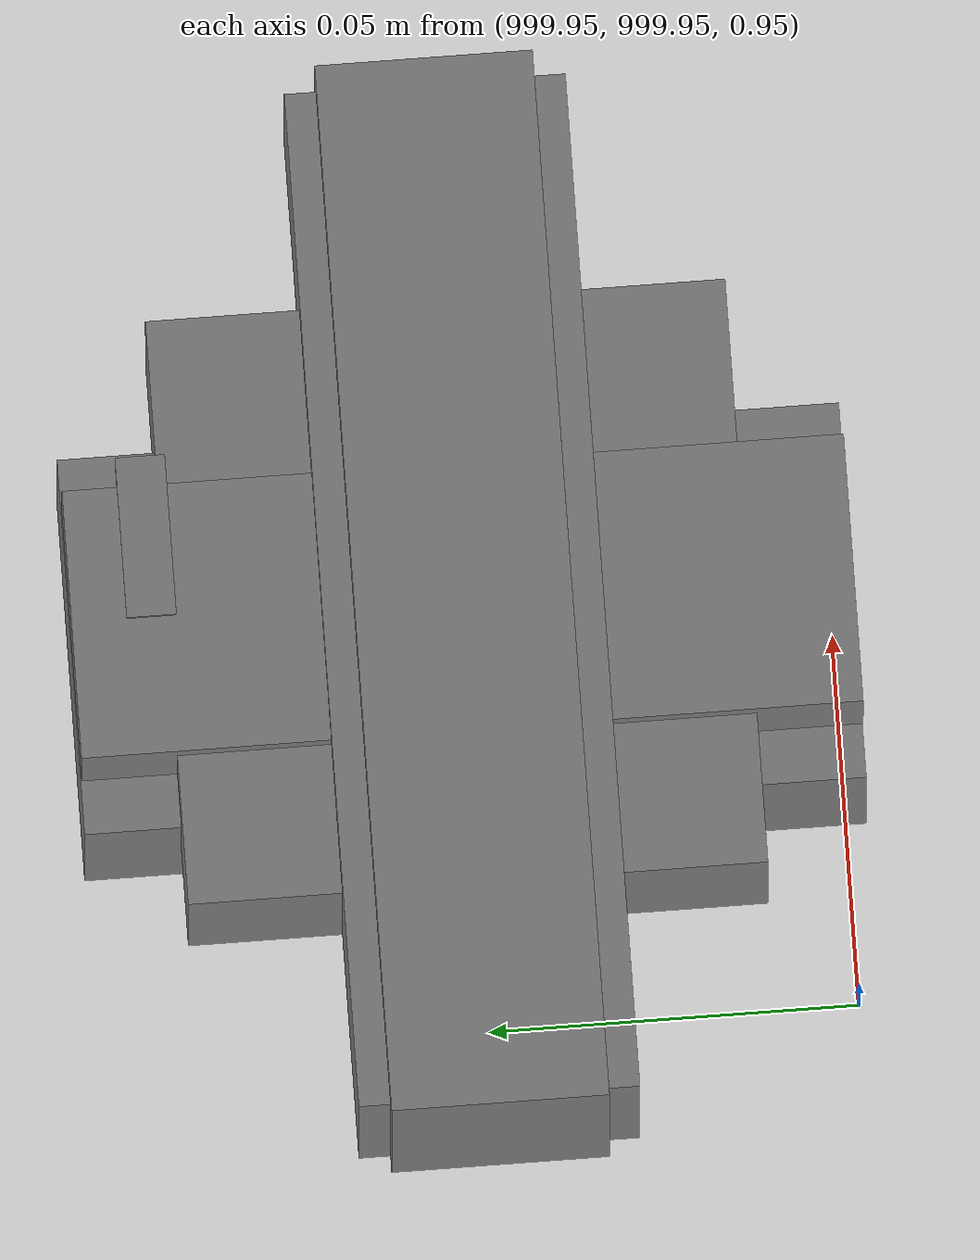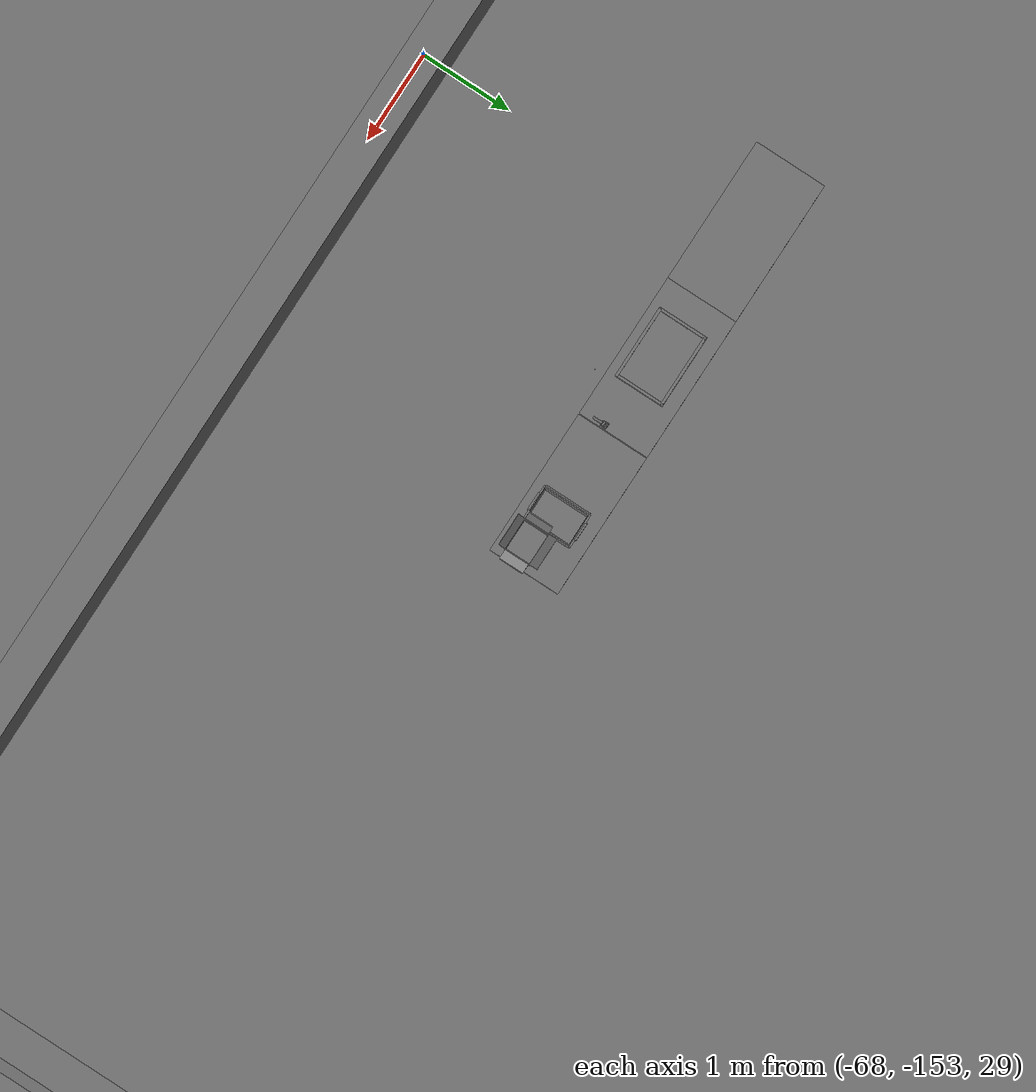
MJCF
<mujoco>
    <option gravity="0.000000000 0.000000000 -9.810000420" timestep="0.0049999999" integrator="implicitfast" density="1.225" viscosity="1.8000001e-05" noslip_iterations="10" iterations="100" sdf_iterations="50">
        <flag multiccd="disable"/>
    </option>
    <size memory="1000M"/>
    <compiler coordinate="local"/>
    <worldbody>
        <light cutoff="30" pos="0 1 1" dir="0 -1 -2"/>
        <light cutoff="30" pos="0 -1 1" dir="0 1 -2"/>
        <body pos="-64.866622925 -149.383972168 30.183746338" euler="89.999984741 89.999946594 0.000000000" name="openloong_gripper_2f85_fix_base_usda_bluebox_01">
            <geom contype="1" conaffinity="1" density="1000" type="box" material="" rgba="0.500000000 0.500000000 0.500000000 1.000000000" solimp="0.899999976 0.949999988 0.001000000" friction="1.000000000 0.005000000 0.000100000" solref="0.020000000 1.000000000" margin="0" condim="3" group="0" pos="0.276580811 0.187225342 0.000068665" quat="0.707106948 0.000077471 0.707106352 0.000077486" size="0.100000001 0.057999998 0.010000000" name="openloong_gripper_2f85_fix_base_usda_geom_E1BBEEE2_7CFF_49A9_82CE_EE9B0D42CCA3"/>
            <geom contype="1" conaffinity="1" density="1000" type="box" material="" rgba="0.500000000 0.500000000 0.500000000 1.000000000" solimp="0.899999976 0.949999988 0.001000000" friction="1.000000000 0.005000000 0.000100000" solref="0.020000000 1.000000000" margin="0" condim="3" group="0" pos="0.000000000 0.002883911 0.000000000" quat="0.999999881 0.000000000 0.000000000 0.000000000" size="0.254000008 0.003000000 0.172000006" name="openloong_gripper_2f85_fix_base_usda_geom_974AC28E_2C05_46B7_A0A1_DC639DEB5EB7"/>
            <geom contype="1" conaffinity="1" density="1000" type="box" material="" rgba="0.500000000 0.500000000 0.500000000 1.000000000" solimp="0.899999976 0.949999988 0.001000000" friction="1.000000000 0.005000000 0.000100000" solref="0.020000000 1.000000000" margin="0" condim="3" group="0" pos="0.000000000 0.124874115 0.173484802" quat="0.999796331 0.020176515 -0.000000015 0.000000030" size="0.259999990 0.119999997 0.007000000" name="openloong_gripper_2f85_fix_base_usda_geom_9F509FFC_5C7C_443E_8985_EB3A6E97BFA3"/>
            <geom contype="1" conaffinity="1" density="1000" type="box" material="" rgba="0.500000000 0.500000000 0.500000000 1.000000000" solimp="0.899999976 0.949999988 0.001000000" friction="1.000000000 0.005000000 0.000100000" solref="0.020000000 1.000000000" margin="0" condim="3" group="0" pos="0.000000000 0.124874115 -0.173469543" quat="0.999796331 -0.020176545 -0.000000015 0.000000000" size="0.259999990 0.119999997 0.007000000" name="openloong_gripper_2f85_fix_base_usda_geom_D988BB65_3D22_4E3C_98DC_12BF873C422B"/>
            <geom contype="1" conaffinity="1" density="1000" type="box" material="" rgba="0.500000000 0.500000000 0.500000000 1.000000000" solimp="0.899999976 0.949999988 0.001000000" friction="1.000000000 0.005000000 0.000100000" solref="0.020000000 1.000000000" margin="0" condim="3" group="0" pos="0.000000000 0.214008331 0.188980103" quat="0.999912977 0.013176724 0.000000015 0.000000000" size="0.259999990 0.029999999 0.012500000" name="openloong_gripper_2f85_fix_base_usda_geom_88F9AE67_CD0C_4559_8E0D_EB0FA118534C"/>
            <geom contype="1" conaffinity="1" density="1000" type="box" material="" rgba="0.500000000 0.500000000 0.500000000 1.000000000" solimp="0.899999976 0.949999988 0.001000000" friction="1.000000000 0.005000000 0.000100000" solref="0.020000000 1.000000000" margin="0" condim="3" group="0" pos="-0.258361816 0.125289917 0.001876831" quat="0.702796936 -0.020792112 0.710783124 0.020769298" size="0.189999998 0.119999997 0.009000000" name="openloong_gripper_2f85_fix_base_usda_geom_78CF1C71_3C77_4EF5_BE3C_935D56A9A7C8"/>
            <geom contype="1" conaffinity="1" density="1000" type="box" material="" rgba="0.500000000 0.500000000 0.500000000 1.000000000" solimp="0.899999976 0.949999988 0.001000000" friction="1.000000000 0.005000000 0.000100000" solref="0.020000000 1.000000000" margin="0" condim="3" group="0" pos="0.000000000 0.214008331 -0.188980103" quat="0.999912977 -0.013176769 0.000000030 0.000000015" size="0.259999990 0.029999999 0.012500000" name="openloong_gripper_2f85_fix_base_usda_geom_0B236C2E_1DB3_43CC_9A4E_E616E9535AD4"/>
            <geom contype="1" conaffinity="1" density="1000" type="box" material="" rgba="0.500000000 0.500000000 0.500000000 1.000000000" solimp="0.899999976 0.949999988 0.001000000" friction="1.000000000 0.005000000 0.000100000" solref="0.020000000 1.000000000" margin="0" condim="3" group="0" pos="-0.276611328 0.187225342 0.000068665" quat="0.707106650 0.000077441 0.707106709 0.000077456" size="0.100000001 0.057999998 0.010000000" name="openloong_gripper_2f85_fix_base_usda_geom_29121441_141F_4A86_B703_D14B97CA3F68"/>
            <geom contype="1" conaffinity="1" density="1000" type="box" material="" rgba="0.500000000 0.500000000 0.500000000 1.000000000" solimp="0.899999976 0.949999988 0.001000000" friction="1.000000000 0.005000000 0.000100000" solref="0.020000000 1.000000000" margin="0" condim="3" group="0" pos="0.258331299 0.125289917 0.001876831" quat="0.702851415 0.018856421 0.710823774 -0.019329369" size="0.189999998 0.119999997 0.009000000" name="openloong_gripper_2f85_fix_base_usda_geom_A2A69F91_D99B_466A_B0E5_A3356E399511"/>
            <freejoint name="openloong_gripper_2f85_fix_base_usda_bluebox_01_joint"/>
            <site size="0.005000000 0.005000000 0.005000000" rgba="0.500000000 0.500000000 0.500000000 1.000000000" pos="0.000000000 0.000000000 0.000000000" quat="0.999961913 0.008726534 0.000000000 0.000000000" group="0" type="sphere" name="openloong_gripper_2f85_fix_base_usda_bluebox_01site"/>
        </body>
        <body pos="-64.496299744 -149.491867065 30.235729218" euler="0.000000000 0.000000000 89.999946594" name="openloong_gripper_2f85_fix_base_usda_cardboardbox_01">
            <geom contype="1" conaffinity="1" density="1000" type="box" material="" rgba="0.500000000 0.500000000 0.500000000 1.000000000" solimp="0.899999976 0.949999988 0.001000000" friction="1.000000000 0.005000000 0.000100000" solref="0.020000000 1.000000000" margin="0" condim="3" group="0" pos="-0.003166199 -0.004086494 0.005052090" quat="1.000000000 0.000000000 0.000000000 0.000000000" size="0.142499998 0.177500010 0.005000000" name="openloong_gripper_2f85_fix_base_usda_geom_A1C1CA0E_7778_4429_8F80_340DD5AE695F"/>
            <geom contype="1" conaffinity="1" density="1000" type="box" material="" rgba="0.500000000 0.500000000 0.500000000 1.000000000" solimp="0.899999976 0.949999988 0.001000000" friction="1.000000000 0.005000000 0.000100000" solref="0.020000000 1.000000000" margin="0" condim="3" group="0" pos="-0.003166199 0.170316696 0.150570869" quat="1.000000000 0.000000000 0.000000000 0.000000000" size="0.142499998 0.005000000 0.149999991" name="openloong_gripper_2f85_fix_base_usda_geom_4B22CF7F_6EB5_4ECD_8EA4_BF1A650ABF1B"/>
            <geom contype="1" conaffinity="1" density="1000" type="box" material="" rgba="0.500000000 0.500000000 0.500000000 1.000000000" solimp="0.899999976 0.949999988 0.001000000" friction="1.000000000 0.005000000 0.000100000" solref="0.020000000 1.000000000" margin="0" condim="3" group="0" pos="-0.147399902 -0.005307198 0.150570869" quat="1.000000000 0.000000000 0.000000000 0.000000000" size="0.005000000 0.177500010 0.149999991" name="openloong_gripper_2f85_fix_base_usda_geom_E8C32850_D57D_4A1D_A302_181CBA089AAE"/>
            <geom contype="1" conaffinity="1" density="1000" type="box" material="" rgba="0.500000000 0.500000000 0.500000000 1.000000000" solimp="0.899999976 0.949999988 0.001000000" friction="1.000000000 0.005000000 0.000100000" solref="0.020000000 1.000000000" margin="0" condim="3" group="0" pos="0.140275955 -0.005307198 0.150570869" quat="1.000000000 0.000000000 0.000000000 0.000000000" size="0.005000000 0.177500010 0.149999991" name="openloong_gripper_2f85_fix_base_usda_geom_249A404D_156F_45CA_894D_E9C463D17EA3"/>
            <geom contype="1" conaffinity="1" density="1000" type="box" material="" rgba="0.500000000 0.500000000 0.500000000 1.000000000" solimp="0.899999976 0.949999988 0.001000000" friction="1.000000000 0.005000000 0.000100000" solref="0.020000000 1.000000000" margin="0" condim="3" group="0" pos="-0.003166199 -0.181550980 0.150570869" quat="1.000000000 0.000000000 0.000000000 0.000000000" size="0.142499998 0.005000000 0.149999991" name="openloong_gripper_2f85_fix_base_usda_geom_D7062E6F_452E_4F5C_A00E_4E19ECB34AA4"/>
            <freejoint name="openloong_gripper_2f85_fix_base_usda_cardboardbox_01_joint"/>
            <site size="0.005000000 0.005000000 0.005000000" rgba="0.500000000 0.500000000 0.500000000 1.000000000" pos="0.000000000 0.000000000 0.000000000" quat="0.999961913 0.008726535 0.000000000 0.000000000" group="0" type="sphere" name="openloong_gripper_2f85_fix_base_usda_site_E84744C7_0EA5_4E61_9F63_732509C0AC0D"/>
            <body pos="0.139160156 -0.004048347 0.301930904" euler="-179.999954224 49.383502960 179.999954224" name="openloong_gripper_2f85_fix_base_usda_A1_006">
                <geom contype="1" conaffinity="1" density="1000" type="box" material="" rgba="0.500000000 0.500000000 0.500000000 1.000000000" solimp="0.899999976 0.949999988 0.001000000" friction="1.000000000 0.005000000 0.000100000" solref="0.020000000 1.000000000" margin="0" condim="3" group="0" pos="-0.071587563 0.000009537 0.001745224" quat="0.999999881 0.000000000 0.000000000 0.000000000" size="0.071249999 0.179999992 0.002500000" name="openloong_gripper_2f85_fix_base_usda_geom_4D31EDD6_7517_40DC_8E64_7E93E0F602FA"/>
                <joint armature="0" stiffness="0.07" damping="0.0099999998" axis="0.000000 1.000000 0.000000" type="hinge" name="openloong_gripper_2f85_fix_base_usda_A1_006"/>
            </body>
            <body pos="-0.145902634 -0.004086494 0.301938057" euler="-180.000000000 -60.000011444 -180.000000000" name="openloong_gripper_2f85_fix_base_usda_A2_006">
                <geom contype="1" conaffinity="1" density="1000" type="box" material="" rgba="0.500000000 0.500000000 0.500000000 1.000000000" solimp="0.899999976 0.949999988 0.001000000" friction="1.000000000 0.005000000 0.000100000" solref="0.020000000 1.000000000" margin="0" condim="3" group="0" pos="0.071268082 0.000009537 0.002717972" quat="0.000002921 0.000000000 -0.000000030 0.999999881" size="0.071249999 0.179999992 0.002500000" name="openloong_gripper_2f85_fix_base_usda_geom_A9B89D68_0AA7_4F60_9A2A_AFA579448B83"/>
                <joint armature="0" stiffness="0.07" damping="0.0099999998" axis="0.000000 1.000000 0.000000" type="hinge" name="openloong_gripper_2f85_fix_base_usda_A2_006"/>
            </body>
            <body pos="-0.003385544 0.175991058 0.301930904" euler="-125.858116150 -0.000004561 0.000002331" name="openloong_gripper_2f85_fix_base_usda_B2_006">
                <geom contype="1" conaffinity="1" density="1000" type="box" material="" rgba="0.500000000 0.500000000 0.500000000 1.000000000" solimp="0.899999976 0.949999988 0.001000000" friction="1.000000000 0.005000000 0.000100000" solref="0.020000000 1.000000000" margin="0" condim="3" group="0" pos="0.000009537 -0.070939064 -0.002470016" quat="0.999614120 0.027776197 -0.000000015 0.000000030" size="0.137500003 0.064999998 0.005000000" name="openloong_gripper_2f85_fix_base_usda_geom_5C2B8ED0_18DA_4C14_B9B5_E66253117D18"/>
                <joint armature="0" stiffness="0.07" damping="0.0099999998" axis="1.000000 0.000000 0.000000" type="hinge" name="openloong_gripper_2f85_fix_base_usda_B2_006"/>
            </body>
            <body pos="-0.003385544 -0.184140205 0.301938057" euler="147.805557251 0.000000000 0.000000000" name="openloong_gripper_2f85_fix_base_usda_B1_006">
                <geom contype="1" conaffinity="1" density="1000" type="box" material="" rgba="0.500000000 0.500000000 0.500000000 1.000000000" solimp="0.899999976 0.949999988 0.001000000" friction="1.000000000 0.005000000 0.000100000" solref="0.020000000 1.000000000" margin="0" condim="3" group="0" pos="-0.000028610 0.070202351 -0.002703667" quat="0.999614179 -0.027776167 0.000000000 0.000000000" size="0.137500003 0.064999998 0.005000000" name="openloong_gripper_2f85_fix_base_usda_geom_72DDFEB9_77AB_4335_9EAE_19F9C9A5931D"/>
                <joint armature="0" stiffness="0.07" damping="0.0099999998" axis="1.000000 0.000000 0.000000" type="hinge" name="openloong_gripper_2f85_fix_base_usda_B1_006"/>
            </body>
        </body>
        <body pos="-65.882858276 -149.481979370 30.229999542" euler="-64.487716675 0.000000000 0.000000000" name="openloong_gripper_2f85_fix_base_usda_Barcode">
            <geom contype="1" conaffinity="1" density="1000" type="box" material="" rgba="0.500000000 0.500000000 0.500000000 1.000000000" solimp="0.899999976 0.949999988 0.001000000" friction="1.000000000 0.005000000 0.000100000" solref="0.020000000 1.000000000" margin="0" condim="3" group="0" pos="0.000000000 0.013038635 0.001419067" quat="0.000000000 0.000000000 0.000000000 1.000000119" size="0.034000002 0.010000000 0.017999999" name="openloong_gripper_2f85_fix_base_usda_geom_5AFA4057_F95A_43E6_A3F6_4107D09EF3D3"/>
            <geom contype="1" conaffinity="1" density="1000" type="box" material="" rgba="0.500000000 0.500000000 0.500000000 1.000000000" solimp="0.899999976 0.949999988 0.001000000" friction="1.000000000 0.005000000 0.000100000" solref="0.020000000 1.000000000" margin="0" condim="3" group="0" pos="0.000000000 -0.035301208 -0.007095337" quat="0.000000000 0.000000000 -0.043619365 0.999048233" size="0.028999999 0.010000000 0.020000000" name="openloong_gripper_2f85_fix_base_usda_geom_3F749A19_E5CA_4A49_80C1_FBC35B0838F3"/>
            <geom contype="1" conaffinity="1" density="1000" type="box" material="" rgba="0.500000000 0.500000000 0.500000000 1.000000000" solimp="0.899999976 0.949999988 0.001000000" friction="1.000000000 0.005000000 0.000100000" solref="0.020000000 1.000000000" margin="0" condim="3" group="0" pos="0.000000000 -0.043411255 -0.011749268" quat="0.922262907 0.386563420 0.000000000 0.000000000" size="0.026000001 0.010000000 0.020000000" name="openloong_gripper_2f85_fix_base_usda_geom_06150BAC_B76E_455D_A84B_C553BD8861B6"/>
            <geom contype="1" conaffinity="1" density="1000" type="box" material="" rgba="0.500000000 0.500000000 0.500000000 1.000000000" solimp="0.899999976 0.949999988 0.001000000" friction="1.000000000 0.005000000 0.000100000" solref="0.020000000 1.000000000" margin="0" condim="3" group="0" pos="0.000000000 -0.016967773 -0.031860352" quat="0.000000000 0.000000000 0.000000000 1.000000119" size="0.008000000 0.010000000 0.013000000" name="openloong_gripper_2f85_fix_base_usda_geom_702DCF6D_9D89_4C5A_BF46_C52F8C8E7E49"/>
            <geom contype="1" conaffinity="1" density="1000" type="box" material="" rgba="0.500000000 0.500000000 0.500000000 1.000000000" solimp="0.899999976 0.949999988 0.001000000" friction="1.000000000 0.005000000 0.000100000" solref="0.020000000 1.000000000" margin="0" condim="3" group="0" pos="0.000000000 -0.001869202 0.000312805" quat="0.953716993 0.300705761 0.000000000 0.000000000" size="0.032000002 0.010000000 0.018999999" name="openloong_gripper_2f85_fix_base_usda_geom_EF327AB6_A596_49CB_9701_995690A7AF61"/>
            <geom contype="1" conaffinity="1" density="1000" type="box" material="" rgba="0.500000000 0.500000000 0.500000000 1.000000000" solimp="0.899999976 0.949999988 0.001000000" friction="1.000000000 0.005000000 0.000100000" solref="0.020000000 1.000000000" margin="0" condim="3" group="0" pos="0.000000000 -0.019531250 -0.003173828" quat="0.953716993 0.300705761 0.000000000 0.000000000" size="0.030999999 0.010000000 0.020000000" name="openloong_gripper_2f85_fix_base_usda_geom_4F627596_6CA5_4D57_8A27_2DF116A1823B"/>
            <geom contype="1" conaffinity="1" density="1000" type="box" material="" rgba="0.500000000 0.500000000 0.500000000 1.000000000" solimp="0.899999976 0.949999988 0.001000000" friction="1.000000000 0.005000000 0.000100000" solref="0.020000000 1.000000000" margin="0" condim="3" group="0" pos="0.000000000 -0.035301208 -0.007095337" quat="0.953716993 0.300705761 0.000000000 0.000000000" size="0.028999999 0.010000000 0.020000000" name="openloong_gripper_2f85_fix_base_usda_geom_A0AF7CE6_4F5E_48D9_AA20_4EEB6A1CC94C"/>
            <geom contype="1" conaffinity="1" density="1000" type="box" material="" rgba="0.500000000 0.500000000 0.500000000 1.000000000" solimp="0.899999976 0.949999988 0.001000000" friction="1.000000000 0.005000000 0.000100000" solref="0.020000000 1.000000000" margin="0" condim="3" group="0" pos="0.000000000 -0.042617798 -0.071121216" quat="0.000000000 0.000000000 0.000000000 1.000000119" size="0.013000000 0.021000000 0.059999999" name="openloong_gripper_2f85_fix_base_usda_geom_AC607602_7FDD_410F_8049_42CA5684265D"/>
            <freejoint name="openloong_gripper_2f85_fix_base_usda_Barcode_joint"/>
            <site size="0.005000000 0.005000000 0.005000000" rgba="0.500000000 0.500000000 0.500000000 1.000000000" pos="0.000000000 0.000000000 0.000000000" quat="1.000000000 0.000000000 0.000000000 0.000000000" group="0" type="sphere" name="openloong_gripper_2f85_fix_base_usda_Barcode_site"/>
        </body>
        <body pos="-66.745018005 -149.392349243 30.184000015" euler="0.000000000 0.000000000 89.999946594" name="[22333804866952]_Basket_01">
            <geom contype="1" conaffinity="1" density="1000" type="box" material="" rgba="0.500000000 0.500000000 0.500000000 1.000000000" solimp="0.899999976 0.949999988 0.001000000" friction="1.000000000 0.005000000 0.000100000" solref="0.020000000 1.000000000" margin="0" condim="3" group="0" pos="-0.052425385 0.389207840 0.089787483" quat="0.707107008 0.000000000 0.000000000 0.707106411" size="0.014249999 0.014249999 0.059999999" name="[22333804866952]_geom_4EF086C1_F3B2_4AF4_A9C2_8F1E07AE984A"/>
            <geom contype="1" conaffinity="1" density="1000" type="box" material="" rgba="0.500000000 0.500000000 0.500000000 1.000000000" solimp="0.899999976 0.949999988 0.001000000" friction="1.000000000 0.005000000 0.000100000" solref="0.020000000 1.000000000" margin="0" condim="3" group="0" pos="0.264015198 -0.133043289 0.089787483" quat="0.707107008 0.000000000 0.000000000 0.707106411" size="0.014249999 0.014249999 0.059999999" name="[22333804866952]_geom_3867BE53_F09A_457D_8FE5_B2568240CEDB"/>
            <geom contype="1" conaffinity="1" density="1000" type="box" material="" rgba="0.500000000 0.500000000 0.500000000 1.000000000" solimp="0.899999976 0.949999988 0.001000000" friction="1.000000000 0.005000000 0.000100000" solref="0.020000000 1.000000000" margin="0" condim="3" group="0" pos="-0.264015198 -0.265548706 0.089793205" quat="0.707107008 0.000000000 0.000000000 0.707106411" size="0.014249999 0.014249999 0.059999999" name="[22333804866952]_geom_62305963_A600_4110_8C0B_C4445CCF9AE9"/>
            <geom contype="1" conaffinity="1" density="1000" type="box" material="" rgba="0.500000000 0.500000000 0.500000000 1.000000000" solimp="0.899999976 0.949999988 0.001000000" friction="1.000000000 0.005000000 0.000100000" solref="0.020000000 1.000000000" margin="0" condim="3" group="0" pos="-0.160263062 -0.389322281 0.089793205" quat="0.707107008 0.000000000 0.000000000 0.707106411" size="0.014249999 0.014249999 0.059999999" name="[22333804866952]_geom_2AAF7373_9745_4264_B497_CCA6D178AA7F"/>
            <geom contype="1" conaffinity="1" density="1000" type="box" material="" rgba="0.500000000 0.500000000 0.500000000 1.000000000" solimp="0.899999976 0.949999988 0.001000000" friction="1.000000000 0.005000000 0.000100000" solref="0.020000000 1.000000000" margin="0" condim="3" group="0" pos="0.162265778 -0.389322281 0.089787483" quat="0.707107008 0.000000000 0.000000000 0.707106411" size="0.014249999 0.014249999 0.059999999" name="[22333804866952]_geom_5E3EF281_3C7B_4F77_8488_04EEEFFFB786"/>
            <geom contype="1" conaffinity="1" density="1000" type="box" material="" rgba="0.500000000 0.500000000 0.500000000 1.000000000" solimp="0.899999976 0.949999988 0.001000000" friction="1.000000000 0.005000000 0.000100000" solref="0.020000000 1.000000000" margin="0" condim="3" group="0" pos="0.264015198 0.389207840 0.089787483" quat="0.707107008 0.000000000 0.000000000 0.707106411" size="0.014249999 0.014249999 0.059999999" name="[22333804866952]_geom_DFBA3254_DF05_4D0E_9341_7B44785C8EAD"/>
            <geom contype="1" conaffinity="1" density="1000" type="box" material="" rgba="0.500000000 0.500000000 0.500000000 1.000000000" solimp="0.899999976 0.949999988 0.001000000" friction="1.000000000 0.005000000 0.000100000" solref="0.020000000 1.000000000" margin="0" condim="3" group="0" pos="-0.264015198 -0.133043289 0.089793205" quat="0.707107008 0.000000000 0.000000000 0.707106411" size="0.014249999 0.014249999 0.059999999" name="[22333804866952]_geom_98C624FB_E47C_4B95_B8C7_53DF515F1BDB"/>
            <geom contype="1" conaffinity="1" density="1000" type="box" material="" rgba="0.500000000 0.500000000 0.500000000 1.000000000" solimp="0.899999976 0.949999988 0.001000000" friction="1.000000000 0.005000000 0.000100000" solref="0.020000000 1.000000000" margin="0" condim="3" group="0" pos="-0.264026642 0.269256592 0.089793205" quat="0.707107008 0.000000000 0.000000000 0.707106411" size="0.014249999 0.014249999 0.059999999" name="[22333804866952]_geom_5C762E3F_5196_4C20_B087_5BE2E682ABEB"/>
            <geom contype="1" conaffinity="1" density="1000" type="box" material="" rgba="0.500000000 0.500000000 0.500000000 1.000000000" solimp="0.899999976 0.949999988 0.001000000" friction="1.000000000 0.005000000 0.000100000" solref="0.020000000 1.000000000" margin="0" condim="3" group="0" pos="0.054462433 0.389207840 0.089787483" quat="0.707107008 0.000000000 0.000000000 0.707106411" size="0.014249999 0.014249999 0.059999999" name="[22333804866952]_geom_BA829A20_30A4_4EBB_B1EF_BDDFD36E5700"/>
            <geom contype="1" conaffinity="1" density="1000" type="box" material="" rgba="0.500000000 0.500000000 0.500000000 1.000000000" solimp="0.899999976 0.949999988 0.001000000" friction="1.000000000 0.005000000 0.000100000" solref="0.020000000 1.000000000" margin="0" condim="3" group="0" pos="0.054462433 -0.389322281 0.089787483" quat="0.707107008 0.000000000 0.000000000 0.707106411" size="0.014249999 0.014249999 0.059999999" name="[22333804866952]_geom_BB7A1862_E0D8_4882_BAAD_302749CF7D2D"/>
            <geom contype="1" conaffinity="1" density="1000" type="box" material="" rgba="0.500000000 0.500000000 0.500000000 1.000000000" solimp="0.899999976 0.949999988 0.001000000" friction="1.000000000 0.005000000 0.000100000" solref="0.020000000 1.000000000" margin="0" condim="3" group="0" pos="0.264015198 0.269256592 0.089793205" quat="0.707107008 0.000000000 0.000000000 0.707106411" size="0.014249999 0.014249999 0.059999999" name="[22333804866952]_geom_8F5862BD_720D_4891_8352_DBD7375066F9"/>
            <geom contype="1" conaffinity="1" density="1000" type="box" material="" rgba="0.500000000 0.500000000 0.500000000 1.000000000" solimp="0.899999976 0.949999988 0.001000000" friction="1.000000000 0.005000000 0.000100000" solref="0.020000000 1.000000000" margin="0" condim="3" group="0" pos="0.264015198 -0.389322281 0.089787483" quat="0.707107008 0.000000000 0.000000000 0.707106411" size="0.014249999 0.014249999 0.059999999" name="[22333804866952]_geom_A1FADA8E_7F93_429C_99F2_A46949506C4B"/>
            <geom contype="1" conaffinity="1" density="1000" type="box" material="" rgba="0.500000000 0.500000000 0.500000000 1.000000000" solimp="0.899999976 0.949999988 0.001000000" friction="1.000000000 0.005000000 0.000100000" solref="0.020000000 1.000000000" margin="0" condim="3" group="0" pos="0.000000000 0.000000000 0.015998840" quat="0.707107008 0.000000000 0.000000000 0.707106411" size="0.403499991 0.279000014 0.015750000" name="[22333804866952]_geom_3C989F3E_609A_4412_B497_E6741DF05637"/>
            <geom contype="1" conaffinity="1" density="1000" type="box" material="" rgba="0.500000000 0.500000000 0.500000000 1.000000000" solimp="0.899999976 0.949999988 0.001000000" friction="1.000000000 0.005000000 0.000100000" solref="0.020000000 1.000000000" margin="0" condim="3" group="0" pos="0.000000000 -0.389476776 0.163619041" quat="0.707107008 0.000000000 0.000000000 0.707106411" size="0.015000000 0.277500004 0.015750000" name="[22333804866952]_geom_78AB7B6F_FC17_48F2_833C_55E8DBEFF753"/>
            <geom contype="1" conaffinity="1" density="1000" type="box" material="" rgba="0.500000000 0.500000000 0.500000000 1.000000000" solimp="0.899999976 0.949999988 0.001000000" friction="1.000000000 0.005000000 0.000100000" solref="0.020000000 1.000000000" margin="0" condim="3" group="0" pos="0.162265778 0.389207840 0.089787483" quat="0.707107008 0.000000000 0.000000000 0.707106411" size="0.014249999 0.014249999 0.059999999" name="[22333804866952]_geom_F55F6AF9_2451_496A_95A2_F1BC57C3DED1"/>
            <geom contype="1" conaffinity="1" density="1000" type="box" material="" rgba="0.500000000 0.500000000 0.500000000 1.000000000" solimp="0.899999976 0.949999988 0.001000000" friction="1.000000000 0.005000000 0.000100000" solref="0.020000000 1.000000000" margin="0" condim="3" group="0" pos="0.000000000 0.389471054 0.163619041" quat="0.707107008 0.000000000 0.000000000 0.707106411" size="0.015000000 0.277500004 0.015750000" name="[22333804866952]_geom_32665B6A_9EB0_4491_B73F_B870986BF33C"/>
            <geom contype="1" conaffinity="1" density="1000" type="box" material="" rgba="0.500000000 0.500000000 0.500000000 1.000000000" solimp="0.899999976 0.949999988 0.001000000" friction="1.000000000 0.005000000 0.000100000" solref="0.020000000 1.000000000" margin="0" condim="3" group="0" pos="-0.263511658 0.000000000 0.163619041" quat="0.707107008 0.000000000 0.000000000 0.707106411" size="0.403499991 0.015000000 0.015750000" name="[22333804866952]_geom_B87B0BE0_006B_487E_BAA8_94D59149FE24"/>
            <geom contype="1" conaffinity="1" density="1000" type="box" material="" rgba="0.500000000 0.500000000 0.500000000 1.000000000" solimp="0.899999976 0.949999988 0.001000000" friction="1.000000000 0.005000000 0.000100000" solref="0.020000000 1.000000000" margin="0" condim="3" group="0" pos="-0.264015198 0.141334534 0.089793205" quat="0.707107008 0.000000000 0.000000000 0.707106411" size="0.014249999 0.014249999 0.059999999" name="[22333804866952]_geom_D00C9D2F_BCF4_45FF_A7D8_88DD7642C3EE"/>
            <geom contype="1" conaffinity="1" density="1000" type="box" material="" rgba="0.500000000 0.500000000 0.500000000 1.000000000" solimp="0.899999976 0.949999988 0.001000000" friction="1.000000000 0.005000000 0.000100000" solref="0.020000000 1.000000000" margin="0" condim="3" group="0" pos="0.264015198 -0.265548706 0.089787483" quat="0.707107008 0.000000000 0.000000000 0.707106411" size="0.014249999 0.014249999 0.059999999" name="[22333804866952]_geom_15797F45_1FF9_4328_95E7_D2B3AA5C0598"/>
            <geom contype="1" conaffinity="1" density="1000" type="box" material="" rgba="0.500000000 0.500000000 0.500000000 1.000000000" solimp="0.899999976 0.949999988 0.001000000" friction="1.000000000 0.005000000 0.000100000" solref="0.020000000 1.000000000" margin="0" condim="3" group="0" pos="-0.160263062 0.389207840 0.089787483" quat="0.707107008 0.000000000 0.000000000 0.707106411" size="0.014249999 0.014249999 0.059999999" name="[22333804866952]_geom_12D041E9_1C50_428D_BC8D_E31D7B732247"/>
            <geom contype="1" conaffinity="1" density="1000" type="box" material="" rgba="0.500000000 0.500000000 0.500000000 1.000000000" solimp="0.899999976 0.949999988 0.001000000" friction="1.000000000 0.005000000 0.000100000" solref="0.020000000 1.000000000" margin="0" condim="3" group="0" pos="-0.052425385 -0.389322281 0.089787483" quat="0.707107008 0.000000000 0.000000000 0.707106411" size="0.014249999 0.014249999 0.059999999" name="[22333804866952]_geom_908F0260_904F_4B01_9C27_D2E746A0AD2E"/>
            <geom contype="1" conaffinity="1" density="1000" type="box" material="" rgba="0.500000000 0.500000000 0.500000000 1.000000000" solimp="0.899999976 0.949999988 0.001000000" friction="1.000000000 0.005000000 0.000100000" solref="0.020000000 1.000000000" margin="0" condim="3" group="0" pos="-0.264026642 -0.389322281 0.089793205" quat="0.707107008 0.000000000 0.000000000 0.707106411" size="0.014249999 0.014249999 0.059999999" name="[22333804866952]_geom_F00F585F_179D_4349_A2DC_2B2235FF7C29"/>
            <geom contype="1" conaffinity="1" density="1000" type="box" material="" rgba="0.500000000 0.500000000 0.500000000 1.000000000" solimp="0.899999976 0.949999988 0.001000000" friction="1.000000000 0.005000000 0.000100000" solref="0.020000000 1.000000000" margin="0" condim="3" group="0" pos="0.264015198 0.141334534 0.089787483" quat="0.707107008 0.000000000 0.000000000 0.707106411" size="0.014249999 0.014249999 0.059999999" name="[22333804866952]_geom_E7F7E4AD_B1C5_48E4_B811_54F4439D3846"/>
            <geom contype="1" conaffinity="1" density="1000" type="box" material="" rgba="0.500000000 0.500000000 0.500000000 1.000000000" solimp="0.899999976 0.949999988 0.001000000" friction="1.000000000 0.005000000 0.000100000" solref="0.020000000 1.000000000" margin="0" condim="3" group="0" pos="-0.264015198 0.389207840 0.089793205" quat="0.707107008 0.000000000 0.000000000 0.707106411" size="0.014249999 0.014249999 0.059999999" name="[22333804866952]_geom_FC2F38A3_1146_48E5_883F_70A888AC4DB0"/>
            <geom contype="1" conaffinity="1" density="1000" type="box" material="" rgba="0.500000000 0.500000000 0.500000000 1.000000000" solimp="0.899999976 0.949999988 0.001000000" friction="1.000000000 0.005000000 0.000100000" solref="0.020000000 1.000000000" margin="0" condim="3" group="0" pos="0.264015198 0.004480362 0.089787483" quat="0.707107008 0.000000000 0.000000000 0.707106411" size="0.014249999 0.014249999 0.059999999" name="[22333804866952]_geom_CF51F1D8_9038_4016_BC1C_FE2309CE61EA"/>
            <geom contype="1" conaffinity="1" density="1000" type="box" material="" rgba="0.500000000 0.500000000 0.500000000 1.000000000" solimp="0.899999976 0.949999988 0.001000000" friction="1.000000000 0.005000000 0.000100000" solref="0.020000000 1.000000000" margin="0" condim="3" group="0" pos="0.263694763 -0.000011444 0.163619041" quat="0.707107008 0.000000000 0.000000000 0.707106411" size="0.403499991 0.015000000 0.015750000" name="[22333804866952]_geom_CE6A88A0_B00D_47EF_AEEA_DA848EA62119"/>
            <geom contype="1" conaffinity="1" density="1000" type="box" material="" rgba="0.500000000 0.500000000 0.500000000 1.000000000" solimp="0.899999976 0.949999988 0.001000000" friction="1.000000000 0.005000000 0.000100000" solref="0.020000000 1.000000000" margin="0" condim="3" group="0" pos="-0.264015198 0.004480362 0.089793205" quat="0.707107008 0.000000000 0.000000000 0.707106411" size="0.014249999 0.014249999 0.059999999" name="[22333804866952]_geom_6A8D2887_65A6_4D34_B94E_0E9BE6FC5CAC"/>
            <freejoint name="[22333804866952]_joint_FDC7CC02_925A_43C3_BCBC_24DACEB14090"/>
        </body>
        <body pos="0.000000000 0.000000000 0.000000000" euler="0.000000000 0.000000000 0.000000000" name="Static Objects_Static Objects">
            <geom contype="1" conaffinity="1" density="1000" type="box" material="" rgba="0.500000000 0.500000000 0.500000000 1.000000000" solimp="0.899999976 0.949999988 0.001000000" friction="1.000000000 0.005000000 0.000100000" solref="0.020000000 1.000000000" margin="0" condim="3" group="0" pos="-67.544113159 -149.365814209 29.727830887" quat="0.500000417 0.499999970 0.499999553 0.499999970" size="0.381000012 0.319999993 0.041000001" name="Static Objects_geom_4C8F8EDA_4F31_4242_8D87_450AB467A8E5"/>
            <geom contype="1" conaffinity="1" density="1000" type="box" material="" rgba="0.500000000 0.500000000 0.500000000 1.000000000" solimp="0.899999976 0.949999988 0.001000000" friction="1.000000000 0.005000000 0.000100000" solref="0.020000000 1.000000000" margin="0" condim="3" group="0" pos="-68.239501953 -149.365814209 30.086868286" quat="0.500000417 0.499999970 0.499999553 0.499999970" size="0.370999992 0.039500002 0.745000005" name="Static Objects_geom_06B8A763_5140_4F33_AACC_D2909823A329"/>
            <geom contype="1" conaffinity="1" density="1000" type="box" material="" rgba="0.500000000 0.500000000 0.500000000 1.000000000" solimp="0.899999976 0.949999988 0.001000000" friction="1.000000000 0.005000000 0.000100000" solref="0.020000000 1.000000000" margin="0" condim="3" group="0" pos="-68.239501953 -149.365814209 30.147235870" quat="0.500000417 0.499999970 0.499999553 0.499999970" size="0.400000006 0.022000000 0.800000012" name="Static Objects_geom_D0D2C29B_0F94_418F_B3CA_627259D1A99D"/>
            <geom contype="1" conaffinity="1" density="1000" type="box" material="" rgba="0.500000000 0.500000000 0.500000000 1.000000000" solimp="0.899999976 0.949999988 0.001000000" friction="1.000000000 0.005000000 0.000100000" solref="0.020000000 1.000000000" margin="0" condim="3" group="0" pos="-68.934890747 -149.365814209 29.727830887" quat="0.500000417 0.499999970 0.499999553 0.499999970" size="0.381000012 0.319999993 0.041000001" name="Static Objects_geom_A6746985_B9C5_4EC2_B613_2A38E6DA2333"/>
            <geom contype="1" conaffinity="1" density="1000" type="box" material="" rgba="0.500000000 0.500000000 0.500000000 1.000000000" solimp="0.899999976 0.949999988 0.001000000" friction="1.000000000 0.005000000 0.000100000" solref="0.020000000 1.000000000" margin="0" condim="3" group="0" pos="-68.239501953 -149.365814209 29.561563492" quat="0.500000417 0.499999970 0.499999553 0.499999970" size="0.020000000 0.022000000 0.660000026" name="Static Objects_geom_88FC4653_FFAE_42B7_A120_61EE80F62490"/>
            <geom contype="1" conaffinity="1" density="1000" type="box" material="" rgba="0.500000000 0.500000000 0.500000000 1.000000000" solimp="0.899999976 0.949999988 0.001000000" friction="1.000000000 0.005000000 0.000100000" solref="0.020000000 1.000000000" margin="0" condim="3" group="0" pos="-65.945671082 -149.365814209 29.727830887" quat="0.500000417 0.499999970 0.499999553 0.499999970" size="0.381000012 0.319999993 0.041000001" name="Static Objects_geom_A096A619_E078_494C_8D31_A9C4A1C4663D"/>
            <geom contype="1" conaffinity="1" density="1000" type="box" material="" rgba="0.500000000 0.500000000 0.500000000 1.000000000" solimp="0.899999976 0.949999988 0.001000000" friction="1.000000000 0.005000000 0.000100000" solref="0.020000000 1.000000000" margin="0" condim="3" group="0" pos="-66.641059875 -149.365814209 30.086868286" quat="0.500000417 0.499999970 0.499999553 0.499999970" size="0.370999992 0.039500002 0.745000005" name="Static Objects_geom_073D5A18_62B3_44FD_B2CB_C3436AA831A1"/>
            <geom contype="1" conaffinity="1" density="1000" type="box" material="" rgba="0.500000000 0.500000000 0.500000000 1.000000000" solimp="0.899999976 0.949999988 0.001000000" friction="1.000000000 0.005000000 0.000100000" solref="0.020000000 1.000000000" margin="0" condim="3" group="0" pos="-66.641059875 -149.365814209 30.147235870" quat="0.500000417 0.499999970 0.499999553 0.499999970" size="0.400000006 0.022000000 0.800000012" name="Static Objects_geom_723BB485_3D89_4A31_8400_8B76215B0EE5"/>
            <geom contype="1" conaffinity="1" density="1000" type="box" material="" rgba="0.500000000 0.500000000 0.500000000 1.000000000" solimp="0.899999976 0.949999988 0.001000000" friction="1.000000000 0.005000000 0.000100000" solref="0.020000000 1.000000000" margin="0" condim="3" group="0" pos="-67.336448669 -149.365814209 29.727830887" quat="0.500000417 0.499999970 0.499999553 0.499999970" size="0.381000012 0.319999993 0.041000001" name="Static Objects_geom_F2AE5406_7A9C_432E_94B3_25095C8B92AA"/>
            <geom contype="1" conaffinity="1" density="1000" type="box" material="" rgba="0.500000000 0.500000000 0.500000000 1.000000000" solimp="0.899999976 0.949999988 0.001000000" friction="1.000000000 0.005000000 0.000100000" solref="0.020000000 1.000000000" margin="0" condim="3" group="0" pos="-66.641059875 -149.365814209 29.561563492" quat="0.500000417 0.499999970 0.499999553 0.499999970" size="0.020000000 0.022000000 0.660000026" name="Static Objects_geom_4EBEF23A_C087_4633_AADC_07B6B2571DEE"/>
            <geom contype="1" conaffinity="1" density="1000" type="box" material="" rgba="0.500000000 0.500000000 0.500000000 1.000000000" solimp="0.899999976 0.949999988 0.001000000" friction="1.000000000 0.005000000 0.000100000" solref="0.020000000 1.000000000" margin="0" condim="3" group="0" pos="-64.338577271 -149.365814209 29.727830887" quat="0.500000417 0.499999970 0.499999553 0.499999970" size="0.381000012 0.319999993 0.041000001" name="Static Objects_geom_DA238F21_7220_4756_AC86_F0B693275AEC"/>
            <geom contype="1" conaffinity="1" density="1000" type="box" material="" rgba="0.500000000 0.500000000 0.500000000 1.000000000" solimp="0.899999976 0.949999988 0.001000000" friction="1.000000000 0.005000000 0.000100000" solref="0.020000000 1.000000000" margin="0" condim="3" group="0" pos="-65.033966064 -149.365814209 30.086868286" quat="0.500000417 0.499999970 0.499999553 0.499999970" size="0.370999992 0.039500002 0.745000005" name="Static Objects_geom_F7E8A7E4_F04C_4E92_AB9B_9810C04068DE"/>
            <geom contype="1" conaffinity="1" density="1000" type="box" material="" rgba="0.500000000 0.500000000 0.500000000 1.000000000" solimp="0.899999976 0.949999988 0.001000000" friction="1.000000000 0.005000000 0.000100000" solref="0.020000000 1.000000000" margin="0" condim="3" group="0" pos="-65.033966064 -149.365814209 30.147235870" quat="0.500000417 0.499999970 0.499999553 0.499999970" size="0.400000006 0.022000000 0.800000012" name="Static Objects_geom_AD0D44CA_3974_43D7_9402_72BE1D8075F4"/>
            <geom contype="1" conaffinity="1" density="1000" type="box" material="" rgba="0.500000000 0.500000000 0.500000000 1.000000000" solimp="0.899999976 0.949999988 0.001000000" friction="1.000000000 0.005000000 0.000100000" solref="0.020000000 1.000000000" margin="0" condim="3" group="0" pos="-65.729354858 -149.365814209 29.727830887" quat="0.500000417 0.499999970 0.499999553 0.499999970" size="0.381000012 0.319999993 0.041000001" name="Static Objects_geom_F5689DB8_21FB_403A_9A5A_15DA4ADBBE7E"/>
            <geom contype="1" conaffinity="1" density="1000" type="box" material="" rgba="0.500000000 0.500000000 0.500000000 1.000000000" solimp="0.899999976 0.949999988 0.001000000" friction="1.000000000 0.005000000 0.000100000" solref="0.020000000 1.000000000" margin="0" condim="3" group="0" pos="-65.033966064 -149.365814209 29.561563492" quat="0.500000417 0.499999970 0.499999553 0.499999970" size="0.020000000 0.022000000 0.660000026" name="Static Objects_geom_C62277AA_30C5_4446_AC35_E4EDDA00862F"/>
            <geom contype="1" conaffinity="1" density="1000" type="box" material="" rgba="0.500000000 0.500000000 0.500000000 1.000000000" solimp="0.899999976 0.949999988 0.001000000" friction="1.000000000 0.005000000 0.000100000" solref="0.020000000 1.000000000" margin="0" condim="3" group="0" pos="-61.754566193 -137.853729248 33.906845093" quat="0.707107067 0.000000000 0.000000000 0.707106471" size="0.759999990 0.759999990 4.500000000" name="Static Objects_geom_55F89C76_2A69_459A_9F98_E0411D5FB793"/>
            <geom contype="1" conaffinity="1" density="1000" type="box" material="" rgba="0.500000000 0.500000000 0.500000000 1.000000000" solimp="0.899999976 0.949999988 0.001000000" friction="1.000000000 0.005000000 0.000100000" solref="0.020000000 1.000000000" margin="0" condim="3" group="0" pos="-57.511135101 -144.927108765 31.707921982" quat="1.000000000 0.000000000 0.000000000 0.000000000" size="0.200000003 8.000000000 2.299999952" name="Static Objects_geom_6C52F4C1_342A_426B_9C6D_87EE943B0393"/>
            <geom contype="1" conaffinity="1" density="1000" type="box" material="" rgba="0.500000000 0.500000000 0.500000000 1.000000000" solimp="0.899999976 0.949999988 0.001000000" friction="1.000000000 0.005000000 0.000100000" solref="0.020000000 1.000000000" margin="0" condim="3" group="0" pos="-80.517646790 -157.574050903 31.688196182" quat="0.707107067 0.000000000 0.000000000 0.707106471" size="0.600000024 0.600000024 2.299999952" name="Static Objects_geom_9A2EB495_024E_47CA_91FB_680757535C6C"/>
            <geom contype="1" conaffinity="1" density="1000" type="box" material="" rgba="0.500000000 0.500000000 0.500000000 1.000000000" solimp="0.899999976 0.949999988 0.001000000" friction="1.000000000 0.005000000 0.000100000" solref="0.020000000 1.000000000" margin="0" condim="3" group="0" pos="-80.711044312 -147.414932251 31.666158676" quat="1.000000000 0.000000000 0.000000000 0.000000000" size="0.200000003 10.000000000 2.299999952" name="Static Objects_geom_2BA4ADDF_A21A_409A_BF7D_15E538B297F5"/>
            <geom contype="1" conaffinity="1" density="1000" type="box" material="" rgba="0.500000000 0.500000000 0.500000000 1.000000000" solimp="0.899999976 0.949999988 0.001000000" friction="1.000000000 0.005000000 0.000100000" solref="0.020000000 1.000000000" margin="0" condim="3" group="0" pos="-57.687217712 -137.434692383 31.688196182" quat="0.707107067 0.000000000 0.000000000 0.707106471" size="0.600000024 0.600000024 2.299999952" name="Static Objects_geom_34925E6D_1486_4EAE_BB89_518E07F36690"/>
            <geom contype="1" conaffinity="1" density="1000" type="box" material="" rgba="0.500000000 0.500000000 0.500000000 1.000000000" solimp="0.899999976 0.949999988 0.001000000" friction="1.000000000 0.005000000 0.000100000" solref="0.020000000 1.000000000" margin="0" condim="3" group="0" pos="-69.537033081 -140.263229370 31.714921951" quat="0.707107067 0.000000000 0.000000000 0.707106471" size="0.759999990 4.500000000 2.299999952" name="Static Objects_geom_949D1D79_2F01_4D7A_A2BD_A9F548A7D98E"/>
            <geom contype="1" conaffinity="1" density="1000" type="box" material="" rgba="0.500000000 0.500000000 0.500000000 1.000000000" solimp="0.899999976 0.949999988 0.001000000" friction="1.000000000 0.005000000 0.000100000" solref="0.020000000 1.000000000" margin="0" condim="3" group="0" pos="-80.073638916 -137.853713989 33.906845093" quat="0.707107067 0.000000000 0.000000000 0.707106471" size="0.759999990 0.759999990 4.500000000" name="Static Objects_geom_F5DABEDF_AE41_4B8E_B8DB_B672DA5222C7"/>
            <geom contype="1" conaffinity="1" density="1000" type="box" material="" rgba="0.500000000 0.500000000 0.500000000 1.000000000" solimp="0.899999976 0.949999988 0.001000000" friction="1.000000000 0.005000000 0.000100000" solref="0.020000000 1.000000000" margin="0" condim="3" group="0" pos="-73.406707764 -155.734664917 31.707921982" quat="1.000000000 0.000000000 0.000000000 0.000000000" size="0.200000003 3.000000000 2.299999952" name="Static Objects_geom_5D3360FC_4414_4110_96EE_82EAF8407B9D"/>
            <geom contype="1" conaffinity="1" density="1000" type="box" material="" rgba="0.500000000 0.500000000 0.500000000 1.000000000" solimp="0.899999976 0.949999988 0.001000000" friction="1.000000000 0.005000000 0.000100000" solref="0.020000000 1.000000000" margin="0" condim="3" group="0" pos="-68.497543335 -137.448257446 31.707921982" quat="0.707107067 0.000000000 0.000000000 0.707106471" size="0.200000003 14.000000000 2.299999952" name="Static Objects_geom_37A9B41A_0175_4136_AB34_C516F98D0F53"/>
            <geom contype="1" conaffinity="1" density="1000" type="cylinder" material="" rgba="0.500000000 0.500000000 0.500000000 1.000000000" solimp="0.899999976 0.949999988 0.001000000" friction="1.000000000 0.005000000 0.000100000" solref="0.020000000 1.000000000" margin="0" condim="3" group="0" pos="-68.868522644 -142.134506226 31.711090088" quat="0.707107067 0.000000000 0.000000000 0.707106471" size="0.509999990 2.299999952 1.000000000" name="Static Objects_geom_E705EBDF_88A8_4DA1_8D35_225A3B2A466C"/>
            <geom contype="1" conaffinity="1" density="1000" type="plane" material="" rgba="0.500000000 0.500000000 0.500000000 1.000000000" solimp="0.899999976 0.949999988 0.001000000" friction="1.000000000 0.005000000 0.000100000" solref="0.020000000 1.000000000" margin="0" condim="3" group="0" pos="-72.873703003 -147.131927490 29.409669876" quat="1.000000000 0.000000000 0.000000000 0.000000000" size="18.000000000 14.000000000 1.000000000" name="Static Objects_geom_4ADC32E5_CA80_4F27_AD27_83CADE38EB6B"/>
            <geom contype="1" conaffinity="1" density="1000" type="box" material="" rgba="0.500000000 0.500000000 0.500000000 1.000000000" solimp="0.899999976 0.949999988 0.001000000" friction="1.000000000 0.005000000 0.000100000" solref="0.020000000 1.000000000" margin="0" condim="3" group="0" pos="-79.943580627 -157.782272339 31.707921982" quat="0.707107067 0.000000000 0.000000000 0.707106471" size="0.200000003 7.000000000 2.299999952" name="Static Objects_geom_5E9B757D_8283_481D_8D68_1DADF5E300C2"/>
            <geom contype="1" conaffinity="1" density="1000" type="box" material="" rgba="0.500000000 0.500000000 0.500000000 1.000000000" solimp="0.899999976 0.949999988 0.001000000" friction="1.000000000 0.005000000 0.000100000" solref="0.020000000 1.000000000" margin="0" condim="3" group="0" pos="-65.421028137 -152.903442383 31.707921982" quat="0.707107067 0.000000000 0.000000000 0.707106471" size="0.200000003 7.800000191 2.299999952" name="Static Objects_geom_5C64291A_905C_49D7_B45E_0687F1F0F6C8"/>
            <geom contype="1" conaffinity="1" density="1000" type="box" material="" rgba="0.500000000 0.500000000 0.500000000 1.000000000" solimp="0.899999976 0.949999988 0.001000000" friction="1.000000000 0.005000000 0.000100000" solref="0.020000000 1.000000000" margin="0" condim="3" group="0" pos="-74.776908875 -149.964416504 31.688196182" quat="1.000000000 0.000000000 0.000000000 0.000000000" size="0.600000024 0.409999996 2.299999952" name="Static Objects_geom_D6F9C07E_02D3_424F_B638_C90F1F61CFFB"/>
            <geom contype="1" conaffinity="1" density="1000" type="cylinder" material="" rgba="0.500000000 0.500000000 0.500000000 1.000000000" solimp="0.899999976 0.949999988 0.001000000" friction="1.000000000 0.005000000 0.000100000" solref="0.020000000 1.000000000" margin="0" condim="3" group="0" pos="-60.161884308 -142.134506226 31.711090088" quat="0.707107067 0.000000000 0.000000000 0.707106471" size="0.509999990 2.299999952 1.000000000" name="Static Objects_geom_1FC9F378_D424_40E2_A479_05F8C7FC6053"/>
            <geom contype="1" conaffinity="1" density="1000" type="cylinder" material="" rgba="0.500000000 0.500000000 0.500000000 1.000000000" solimp="0.899999976 0.949999988 0.001000000" friction="1.000000000 0.005000000 0.000100000" solref="0.020000000 1.000000000" margin="0" condim="3" group="0" pos="-75.382453918 -149.963455200 31.711090088" quat="0.707107067 0.000000000 0.000000000 0.707106471" size="0.409999996 2.299999952 1.000000000" name="Static Objects_geom_5EE164B5_E4B4_4EEA_8109_A53916DC6D4A"/>
            <geom contype="1" conaffinity="1" density="1000" type="cylinder" material="" rgba="0.500000000 0.500000000 0.500000000 1.000000000" solimp="0.899999976 0.949999988 0.001000000" friction="1.000000000 0.005000000 0.000100000" solref="0.020000000 1.000000000" margin="0" condim="3" group="0" pos="-74.154960632 -149.963455200 31.711090088" quat="0.707107067 0.000000000 0.000000000 0.707106471" size="0.409999996 2.299999952 1.000000000" name="Static Objects_geom_A4773D35_B2A5_4667_89F2_5124AF0DC559"/>
            <geom contype="1" conaffinity="1" density="1000" type="cylinder" material="" rgba="0.500000000 0.500000000 0.500000000 1.000000000" solimp="0.899999976 0.949999988 0.001000000" friction="1.000000000 0.005000000 0.000100000" solref="0.020000000 1.000000000" margin="0" condim="3" group="0" pos="-77.566612244 -142.134506226 31.711090088" quat="0.707107067 0.000000000 0.000000000 0.707106471" size="0.509999990 2.299999952 1.000000000" name="Static Objects_geom_1C3F472B_3EEA_43D7_A494_EE3159393745"/>
        </body>
        <body pos="1000.000000000 1000.000000000 1.000000000" euler="0.000000000 0.000000000 180.000000000" name="openloong_gripper_2f85_fix_base_usda_wifi_box">
            <geom contype="1" conaffinity="1" density="1000" type="box" material="" rgba="0.500000000 0.500000000 0.500000000 1.000000000" solimp="0.899999976 0.949999988 0.001000000" friction="1.000000000 0.005000000 0.000100000" solref="0.020000000 1.000000000" margin="0" condim="3" group="0" pos="0.000000000 0.000000000 0.058978677" quat="0.000000000 0.000000047 0.000000000 1.000000000" size="0.068499997 0.018999999 0.059000000" name="openloong_gripper_2f85_fix_base_usda_geom_ADBF69F8_E405_42EE_81AF_D8D4C4BAD21A"/>
            <freejoint name="openloong_gripper_2f85_fix_base_usda_wifi_box_joint"/>
            <site size="0.005000000 0.005000000 0.005000000" rgba="0.500000000 0.500000000 0.500000000 1.000000000" pos="0.000000000 0.000000000 0.000000000" quat="0.999961913 0.008726500 0.000000000 0.000000000" group="0" type="sphere" name="openloong_gripper_2f85_fix_base_usda_wifi_boxsite"/>
        </body>
        <body pos="-66.179763794 -149.415115356 31.163385391" euler="-10.005120277 31.147600174 98.848442078" mocap="true" name="spotlight6_SpotLight"/>
        <body pos="1000.000000000 999.999938965 1.000000000" euler="0.000000000 0.000000000 180.000000000" name="openloong_gripper_2f85_fix_base_usda_intelcore_i5">
            <geom contype="1" conaffinity="1" density="1000" type="box" material="" rgba="0.500000000 0.500000000 0.500000000 1.000000000" solimp="0.899999976 0.949999988 0.001000000" friction="1.000000000 0.005000000 0.000100000" solref="0.020000000 1.000000000" margin="0" condim="3" group="0" pos="0.000000000 0.000000000 0.051722717" quat="0.707106709 0.000000000 0.000000000 -0.707106769" size="0.052800000 0.018080002 0.052800000" name="openloong_gripper_2f85_fix_base_usda_geom_7E604A94_1164_4940_BF7E_6C58670A5411"/>
            <freejoint name="openloong_gripper_2f85_fix_base_usda_intelcore_i5_joint"/>
            <site size="0.005000000 0.005000000 0.005000000" rgba="0.500000000 0.500000000 0.500000000 1.000000000" pos="0.000000000 0.000000000 0.000000000" quat="0.999961913 0.008726534 0.000000000 0.000000000" group="0" type="sphere" name="openloong_gripper_2f85_fix_base_usda_intelcore_i5site"/>
        </body>
        <body pos="1000.000000000 1000.000000000 1.000000000" euler="0.000011953 0.000005123 -179.999984741" name="openloong_gripper_2f85_fix_base_usda_intel_box">
            <geom contype="1" conaffinity="1" density="1000" type="box" material="" rgba="0.500000000 0.500000000 0.500000000 1.000000000" solimp="0.899999976 0.949999988 0.001000000" friction="1.000000000 0.005000000 0.000100000" solref="0.020000000 1.000000000" margin="0" condim="3" group="0" pos="0.000000000 -0.000067139 0.000082284" quat="0.707106709 0.000000225 0.000000253 0.707106650" size="0.052800003 0.025300000 0.052800003" name="openloong_gripper_2f85_fix_base_usda_geom_55EA1CD7_F851_4B76_A594_7C1621C8E12A"/>
            <freejoint name="openloong_gripper_2f85_fix_base_usda_intel_box_joint"/>
            <site size="0.005000000 0.005000000 0.005000000" rgba="0.500000000 0.500000000 0.500000000 1.000000000" pos="0.000000000 0.000000000 0.000000000" quat="0.999961913 0.008726500 0.000000000 0.000000000" group="0" type="sphere" name="openloong_gripper_2f85_fix_base_usda_intel_boxsite"/>
        </body>
        <body pos="1000.000000000 1000.000000000 1.000000000" euler="0.000000000 0.000000000 180.000000000" name="openloong_gripper_2f85_fix_base_usda_cpu_fan">
            <geom contype="1" conaffinity="1" density="1000" type="box" material="" rgba="0.500000000 0.500000000 0.500000000 1.000000000" solimp="0.899999976 0.949999988 0.001000000" friction="1.000000000 0.005000000 0.000100000" solref="0.020000000 1.000000000" margin="0" condim="3" group="0" pos="0.000000000 0.000000000 0.070034981" quat="0.000000000 0.000000000 0.000000000 1.000000000" size="0.070700005 0.014699999 0.070700005" name="openloong_gripper_2f85_fix_base_usda_geom_D9713B1E_A6B0_4A2A_9125_BDE29FCBF292"/>
            <freejoint name="openloong_gripper_2f85_fix_base_usda_cpu_fan_joint"/>
            <site size="0.005000000 0.005000000 0.005000000" rgba="0.500000000 0.500000000 0.500000000 1.000000000" pos="0.000000000 0.000000000 0.000000000" quat="0.999961913 0.008726535 0.000000000 0.000000000" group="0" type="sphere" name="openloong_gripper_2f85_fix_base_usda_cpu_fancsite"/>
        </body>
        <body pos="-65.811164856 -149.102416992 31.163373947" euler="-156.182266235 -65.017379761 -14.864285469" mocap="true" name="spotlight3_SpotLight"/>
        <body pos="1000.000000000 1000.000000000 1.000000000" euler="0.000000000 0.000000000 180.000000000" name="openloong_gripper_2f85_fix_base_usda_battery_01">
            <geom contype="1" conaffinity="1" density="1000" type="box" material="" rgba="0.500000000 0.500000000 0.500000000 1.000000000" solimp="0.899999976 0.949999988 0.001000000" friction="1.000000000 0.005000000 0.000100000" solref="0.020000000 1.000000000" margin="0" condim="3" group="0" pos="-0.011123657 -0.041940309 0.101691343" quat="1.000000000 0.000000000 0.000000000 0.000000000" size="0.010800000 0.003375000 0.004725000" name="openloong_gripper_2f85_fix_base_usda_geom_F17402C0_F94B_443C_A1DE_EC128724D176"/>
            <geom contype="1" conaffinity="1" density="1000" type="box" material="" rgba="0.500000000 0.500000000 0.500000000 1.000000000" solimp="0.899999976 0.949999988 0.001000000" friction="1.000000000 0.005000000 0.000100000" solref="0.020000000 1.000000000" margin="0" condim="3" group="0" pos="-0.010876465 -0.044247437 0.047066893" quat="0.998702705 -0.050920475 0.000000000 0.000000000" size="0.009450001 0.002700000 0.024975000" name="openloong_gripper_2f85_fix_base_usda_geom_E6D19175_CDE4_4C62_B446_D3A9171E9C8B"/>
            <geom contype="1" conaffinity="1" density="1000" type="box" material="" rgba="0.500000000 0.500000000 0.500000000 1.000000000" solimp="0.899999976 0.949999988 0.001000000" friction="1.000000000 0.005000000 0.000100000" solref="0.020000000 1.000000000" margin="0" condim="3" group="0" pos="-0.001235962 -0.000659180 0.047381196" quat="1.000000000 0.000000000 0.000000000 0.000000000" size="0.039420001 0.039150000 0.047250003" name="openloong_gripper_2f85_fix_base_usda_geom_451E6544_41C1_4AE5_A451_538043B12D3A"/>
            <geom contype="1" conaffinity="1" density="1000" type="box" material="" rgba="0.500000000 0.500000000 0.500000000 1.000000000" solimp="0.899999976 0.949999988 0.001000000" friction="1.000000000 0.005000000 0.000100000" solref="0.020000000 1.000000000" margin="0" condim="3" group="0" pos="-0.010876465 -0.039138794 0.009851727" quat="1.000000000 0.000000000 0.000000000 0.000000000" size="0.009450001 0.010800000 0.013500000" name="openloong_gripper_2f85_fix_base_usda_geom_7FBCC088_5E79_42AD_95DB_1E4DB91546FE"/>
            <geom contype="1" conaffinity="1" density="1000" type="box" material="" rgba="0.500000000 0.500000000 0.500000000 1.000000000" solimp="0.899999976 0.949999988 0.001000000" friction="1.000000000 0.005000000 0.000100000" solref="0.020000000 1.000000000" margin="0" condim="3" group="0" pos="-0.010876465 -0.041528322 0.071508206" quat="1.000000000 0.000000000 0.000000000 0.000000000" size="0.009450001 0.002700000 0.027000001" name="openloong_gripper_2f85_fix_base_usda_geom_2AC78339_E0F4_4880_B0B6_75CECE45FF3A"/>
            <freejoint name="openloong_gripper_2f85_fix_base_usda_battery_01_joint"/>
            <site size="0.005000000 0.005000000 0.005000000" rgba="0.500000000 0.500000000 0.500000000 1.000000000" pos="0.000000000 0.000000000 0.000000000" quat="0.999961913 0.008726500 0.000000000 0.000000000" group="0" type="sphere" name="openloong_gripper_2f85_fix_base_usda_battery_01site"/>
        </body>
        <body pos="-66.147262573 -149.142089844 31.162212372" euler="-131.227310181 -81.006721497 100.673164368" mocap="true" name="spotlight4_SpotLight"/>
        <body pos="-66.291030884 -149.869689941 29.018842697" euler="0.000000000 0.000000000 89.999946594" mocap="true" name="openloong_gripper_2f85_fix_base_usda_leftHandMocap"/>
        <body pos="-66.291030884 -149.869689941 29.018842697" euler="0.000000000 0.000000000 89.999946594" mocap="true" name="openloong_gripper_2f85_fix_base_usda_rightHandMocap"/>
        <body pos="-66.291030884 -149.869689941 30.218843460" euler="0.000000000 0.000000000 89.999946594" name="openloong_gripper_2f85_fix_base_usda_base_link">
            <geom contype="1" conaffinity="1" density="1000" type="mesh" material="" rgba="0.783999979 0.783999979 0.783999979 1.000000000" solimp="0.899999976 0.949999988 0.001000000" friction="1.000000000 0.005000000 0.000100000" solref="0.020000000 1.000000000" margin="0" condim="3" group="3" mesh="base_link" pos="0.000000000 0.000000000 0.000000000" quat="1.000000000 0.000000000 0.000000000 0.000000000" size="1.000000000 1.000000000 1.000000000" name="openloong_gripper_2f85_fix_base_usda__geom_7_FFEEBF46_D0FC_4CA4_8807_12F8C4DAA744"/>
            <site size="0.005000000 0.005000000 0.005000000" rgba="0.500000000 0.500000000 0.500000000 1.000000000" pos="0.000000000 0.000000000 0.000000000" quat="1.000000000 0.000000000 0.000000000 0.000000000" group="0" type="sphere" name="openloong_gripper_2f85_fix_base_usda_imu"/>
            <inertial mass="22.447001" pos="-0.005664100 -0.001336700 0.238289997" diaginertia="0.374352545 0.277180195 0.220617250" quat="0.999247074 0.035235517 -0.015086859 0.006023135"/>
            <body pos="0.000000000 0.000000000 0.299997330" euler="0.000000000 0.000000000 0.000000000" name="openloong_gripper_2f85_fix_base_usda_dummy_body">
                <geom contype="1" conaffinity="1" density="1000" type="sphere" material="" rgba="0.783999979 0.783999979 0.783999979 1.000000000" solimp="0.899999976 0.949999988 0.001000000" friction="1.000000000 0.005000000 0.000100000" solref="0.020000000 1.000000000" margin="0" condim="3" group="3" pos="0.000000000 0.000000000 0.000000000" quat="1.000000000 0.000000000 0.000000000 0.000000000" size="0.010000000 0.000000000 0.000000000" name="openloong_gripper_2f85_fix_base_usda__geom_8_A920013D_2B51_4BF0_A80A_525DAAFE4B74"/>
                <joint armature="0.0099999998" stiffness="0" damping="0.1" axis="0.000000 0.000000 1.000000" type="hinge" name="openloong_gripper_2f85_fix_base_usda_dummy_joint"/>
                <site size="0.010000000 0.005000000 0.005000000" rgba="0.500000000 0.500000000 0.500000000 1.000000000" pos="0.000000000 0.000000000 0.000000000" quat="1.000000000 0.000000000 0.000000000 0.000000000" group="3" type="sphere" name="openloong_gripper_2f85_fix_base_usda_dummy_site"/>
            </body>
            <body pos="0.009002686 0.000000000 0.406400681" euler="0.000000000 0.000000000 0.000000000" name="openloong_gripper_2f85_fix_base_usda_Link_head_yaw">
                <geom contype="1" conaffinity="1" density="1000" type="mesh" material="" rgba="0.783999979 0.783999979 0.783999979 1.000000000" solimp="0.899999976 0.949999988 0.001000000" friction="1.000000000 0.005000000 0.000100000" solref="0.020000000 1.000000000" margin="0" condim="3" group="3" mesh="Link_head_yaw" pos="0.000000000 0.000000000 0.000000000" quat="1.000000000 0.000000000 0.000000000 0.000000000" size="1.000000000 1.000000000 1.000000000" name="openloong_gripper_2f85_fix_base_usda__geom_10_22E121B4_6DE7_4D41_8EE6_AA22C97B36C3"/>
                <inertial mass="0.84249002" pos="0.000000000 -0.002081400 0.044801001" diaginertia="0.000700588 0.000629000 0.000553812" quat="0.706933022 -0.015675601 0.015677100 0.706933022"/>
                <body pos="0.000000000 -0.034599304 0.048500061" euler="0.000000000 0.000000000 0.000000000" name="openloong_gripper_2f85_fix_base_usda_Link_head_pitch">
                    <geom contype="1" conaffinity="1" density="1000" type="mesh" material="" rgba="0.783999979 0.783999979 0.783999979 1.000000000" solimp="0.899999976 0.949999988 0.001000000" friction="1.000000000 0.005000000 0.000100000" solref="0.020000000 1.000000000" margin="0" condim="3" group="3" mesh="Link_head_pitch" pos="0.000000000 0.000000000 0.000000000" quat="1.000000000 0.000000000 0.000000000 0.000000000" size="1.000000000 1.000000000 1.000000000" name="openloong_gripper_2f85_fix_base_usda__geom_12_4276E8EC_B684_4096_8BE0_CC15BB181ED2"/>
                    <inertial mass="1.3943" pos="0.020569000 0.033004001 0.125000000" diaginertia="0.006381400 0.006289940 0.004481460" quat="0.973390222 0.008406822 0.228157058 0.019624906"/>
                    <body pos="0.000000000 0.029998779 0.000000000" euler="0.000000000 0.000000000 0.000000000" name="openloong_gripper_2f85_fix_base_usda_neck_center_body">
                        <site size="0.010000000 0.005000000 0.005000000" rgba="0.500000000 0.500000000 0.500000000 1.000000000" pos="0.000000000 0.000000000 0.000000000" quat="1.000000000 0.000000000 0.000000000 0.000000000" group="3" type="sphere" name="openloong_gripper_2f85_fix_base_usda_neck_center_site"/>
                        <body pos="0.020004272 0.000000000 0.149999619" euler="-0.000002229 39.998176575 -90.000205994" name="openloong_gripper_2f85_fix_base_usda_camera_head">
                            <site size="0.010000000 0.005000000 0.005000000" rgba="0.500000000 0.500000000 0.500000000 1.000000000" pos="0.000000000 0.000000000 0.000000000" quat="1.000000000 0.000000000 0.000000000 0.000000000" group="3" type="sphere" name="openloong_gripper_2f85_fix_base_usda_camera_head_site"/>
                        </body>
                    </body>
                </body>
            </body>
            <body pos="0.003997803 -0.161598206 0.392200470" euler="0.000000000 0.000000000 0.000000000" name="openloong_gripper_2f85_fix_base_usda_Link_arm_r_01">
                <geom contype="1" conaffinity="1" density="1000" type="mesh" material="" rgba="0.783999979 0.783999979 0.783999979 1.000000000" solimp="0.899999976 0.949999988 0.001000000" friction="1.000000000 0.005000000 0.000100000" solref="0.020000000 1.000000000" margin="0" condim="3" group="3" mesh="Link_arm_r_01" pos="0.000000000 0.000000000 0.000000000" quat="1.000000000 0.000000000 0.000000000 0.000000000" size="1.000000000 1.000000000 1.000000000" name="openloong_gripper_2f85_fix_base_usda__geom_14_E9501518_F71A_4342_825E_F26DFFD768FD"/>
                <joint armature="0.0099999998" stiffness="0" damping="1" axis="0.000000 -1.000000 0.000000" limited="true" range="-170.000015259 170.000015259" type="hinge" name="openloong_gripper_2f85_fix_base_usda_J_arm_r_01"/>
                <inertial mass="0.75641" pos="0.004494600 -0.038293999 -0.000001874" diaginertia="0.000842990 0.000803050 0.000587120" quat="-0.000163502 0.707098067 0.000812463 0.707115054"/>
                <body pos="-0.041992188 -0.041000366 0.000000000" euler="0.000000000 0.000000000 0.000000000" name="openloong_gripper_2f85_fix_base_usda_Link_arm_r_02">
                    <geom contype="1" conaffinity="1" density="1000" type="mesh" material="" rgba="0.783999979 0.783999979 0.783999979 1.000000000" solimp="0.899999976 0.949999988 0.001000000" friction="1.000000000 0.005000000 0.000100000" solref="0.020000000 1.000000000" margin="0" condim="3" group="3" mesh="Link_arm_r_02" pos="0.000000000 0.000000000 0.000000000" quat="1.000000000 0.000000000 0.000000000 0.000000000" size="1.000000000 1.000000000 1.000000000" name="openloong_gripper_2f85_fix_base_usda__geom_16_AD63D559_BB39_4565_B4A5_7258C04F065B"/>
                    <joint armature="0.0099999998" stiffness="0" damping="1" axis="-1.000000 0.000000 0.000000" limited="true" range="-105.000244141 105.000244141" type="hinge" name="openloong_gripper_2f85_fix_base_usda_J_arm_r_02"/>
                    <inertial mass="0.98500001" pos="0.041999999 -0.067430697 0.000000000" diaginertia="0.002262690 0.001730990 0.001154020" quat="0.500000000 0.500000000 -0.500000000 0.500000000"/>
                    <body pos="0.041992188 -0.122596741 0.000000000" euler="0.000000000 0.000000000 0.000000000" name="openloong_gripper_2f85_fix_base_usda_Link_arm_r_03">
                        <geom contype="1" conaffinity="1" density="1000" type="mesh" material="" rgba="0.783999979 0.783999979 0.783999979 1.000000000" solimp="0.899999976 0.949999988 0.001000000" friction="1.000000000 0.005000000 0.000100000" solref="0.020000000 1.000000000" margin="0" condim="3" group="3" mesh="Link_arm_r_03" pos="0.000000000 0.000000000 0.000000000" quat="1.000000000 0.000000000 0.000000000 0.000000000" size="1.000000000 1.000000000 1.000000000" name="openloong_gripper_2f85_fix_base_usda__geom_18_20F9CB91_D05E_425B_8307_D508FC4283B8"/>
                        <joint armature="0.0099999998" stiffness="0" damping="1" axis="0.000000 -1.000000 0.000000" limited="true" range="-170.000015259 170.000015259" type="hinge" name="openloong_gripper_2f85_fix_base_usda_J_arm_r_03"/>
                        <inertial mass="0.95899999" pos="-0.001413580 -0.164663002 0.020757901" diaginertia="0.002101340 0.002064590 0.000754802" quat="0.560480952 0.454391927 -0.443732947 0.531497955"/>
                        <body pos="0.035293579 -0.177406311 0.023998260" euler="0.000000000 0.000000000 0.000000000" name="openloong_gripper_2f85_fix_base_usda_Link_arm_r_04">
                            <geom contype="1" conaffinity="1" density="1000" type="mesh" material="" rgba="0.783999979 0.783999979 0.783999979 1.000000000" solimp="0.899999976 0.949999988 0.001000000" friction="1.000000000 0.005000000 0.000100000" solref="0.020000000 1.000000000" margin="0" condim="3" group="3" mesh="Link_arm_r_04" pos="0.000000000 0.000000000 0.000000000" quat="1.000000000 0.000000000 0.000000000 0.000000000" size="1.000000000 1.000000000 1.000000000" name="openloong_gripper_2f85_fix_base_usda__geom_20_D284FBC7_DD42_4227_A900_63EFCDE6C047"/>
                            <joint armature="0.0099999998" stiffness="0" damping="1" axis="-1.000000 0.000000 0.000000" limited="true" range="0.000000000 170.000015259" type="hinge" name="openloong_gripper_2f85_fix_base_usda_J_arm_r_04"/>
                            <inertial mass="0.60000002" pos="-0.038727000 -0.060766999 -0.021003000" diaginertia="0.001092610 0.000712422 0.000645102" quat="0.327701002 0.632602990 -0.467366993 0.523443997"/>
                            <body pos="-0.035293579 -0.103492737 -0.023998260" euler="0.000000000 0.000000000 0.000000000" name="openloong_gripper_2f85_fix_base_usda_Link_arm_r_05">
                                <geom contype="1" conaffinity="1" density="1000" type="mesh" material="" rgba="0.783999979 0.783999979 0.783999979 1.000000000" solimp="0.899999976 0.949999988 0.001000000" friction="1.000000000 0.005000000 0.000100000" solref="0.020000000 1.000000000" margin="0" condim="3" group="3" mesh="Link_arm_r_05" pos="0.000000000 0.000000000 0.000000000" quat="1.000000000 0.000000000 0.000000000 0.000000000" size="1.000000000 1.000000000 1.000000000" name="openloong_gripper_2f85_fix_base_usda__geom_22_73C4141C_5C4A_41E2_A75F_71721CABB67C"/>
                                <joint armature="0.0099999998" stiffness="0" damping="1" axis="0.000000 -1.000000 0.000000" limited="true" range="-170.000015259 170.000015259" type="hinge" name="openloong_gripper_2f85_fix_base_usda_J_arm_r_05"/>
                                <inertial mass="0.68976003" pos="0.000032712 -0.068658002 -0.000111780" diaginertia="0.002522510 0.002411100 0.000448695" quat="0.707660973 0.706543028 -0.002603360 0.002470550"/>
                                <body pos="-0.026489258 -0.196502686 0.000000000" euler="0.000000000 0.000000000 0.000000000" name="openloong_gripper_2f85_fix_base_usda_Link_arm_r_06">
                                    <geom contype="1" conaffinity="1" density="1000" type="mesh" material="" rgba="0.783999979 0.783999979 0.783999979 1.000000000" solimp="0.899999976 0.949999988 0.001000000" friction="1.000000000 0.005000000 0.000100000" solref="0.020000000 1.000000000" margin="0" condim="3" group="3" mesh="Link_arm_r_06" pos="0.000000000 0.000000000 0.000000000" quat="1.000000000 0.000000000 0.000000000 0.000000000" size="1.000000000 1.000000000 1.000000000" name="openloong_gripper_2f85_fix_base_usda__geom_24_F475D68A_ECC7_416A_B923_BA27F91B495F"/>
                                    <joint armature="0.0099999998" stiffness="0" damping="1" axis="1.000000 0.000000 0.000000" limited="true" range="-105.000244141 105.000244141" type="hinge" name="openloong_gripper_2f85_fix_base_usda_J_arm_r_06"/>
                                    <inertial mass="0.28" pos="0.026078001 -0.000000896 0.001663700" diaginertia="0.000156930 0.000145601 0.000104979" quat="0.707080841 0.001851080 0.001883810 0.707127810"/>
                                    <body pos="0.026489258 0.000000000 0.031799316" euler="0.000000000 0.000000000 0.000000000" name="openloong_gripper_2f85_fix_base_usda_Link_arm_r_07">
                                        <geom contype="1" conaffinity="1" density="1000" type="mesh" material="" rgba="0.783999979 0.783999979 0.783999979 1.000000000" solimp="0.899999976 0.949999988 0.001000000" friction="1.000000000 0.005000000 0.000100000" solref="0.020000000 1.000000000" margin="0" condim="3" group="3" mesh="Link_arm_r_07" pos="0.000000000 0.000000000 0.000000000" quat="1.000000000 0.000000000 0.000000000 0.000000000" size="1.000000000 1.000000000 1.000000000" name="openloong_gripper_2f85_fix_base_usda__geom_26_DF3F825A_45D8_4F3D_995A_4BC92FD82696"/>
                                        <joint armature="0.0099999998" stiffness="0" damping="1" axis="0.000000 0.000000 1.000000" limited="true" range="-60.000133514 60.000133514" type="hinge" name="openloong_gripper_2f85_fix_base_usda_J_arm_r_07"/>
                                        <inertial mass="0.61353999" pos="-0.007859000 -0.158170000 -0.027736001" diaginertia="0.003037610 0.002570910 0.000729379" quat="0.427542925 0.443532884 -0.553093910 0.560867906"/>
                                        <body pos="0.000000000 0.286994934 -0.270000458" euler="150.000350952 -0.000001649 -0.000000442" name="openloong_gripper_2f85_fix_base_usda_camera_wrist_r">
                                            <site size="0.010000000 0.005000000 0.005000000" rgba="0.500000000 0.500000000 0.500000000 1.000000000" pos="0.000000000 0.000000000 0.000000000" quat="1.000000000 0.000000000 0.000000000 0.000000000" group="3" type="sphere" name="openloong_gripper_2f85_fix_base_usda_camera_wrist_r_site"/>
                                        </body>
                                        <body pos="0.000000000 -0.220008850 -0.033002853" euler="0.000000000 0.000000000 179.999969482" name="openloong_gripper_2f85_fix_base_usda_ee_center_body_r">
                                            <site size="0.010000000 0.005000000 0.005000000" rgba="0.500000000 0.500000000 0.500000000 1.000000000" pos="0.000000000 0.000000000 0.000000000" quat="1.000000000 0.000000000 0.000000000 0.000000000" group="3" type="sphere" name="openloong_gripper_2f85_fix_base_usda_ee_center_site_r"/>
                                        </body>
                                        <body pos="0.000000000 -0.066001892 -0.031000137" euler="89.999984741 0.000000000 180.000000000" name="openloong_gripper_2f85_fix_base_usda_zbr_base_link">
                                            <geom contype="1" conaffinity="1" density="1000" type="mesh" material="" rgba="0.783999979 0.783999979 0.783999979 1.000000000" solimp="0.899999976 0.949999988 0.001000000" friction="1.000000000 0.005000000 0.000100000" solref="0.020000000 1.000000000" margin="0" condim="3" group="3" mesh="base" pos="0.000000000 0.000003815 -0.000007629" quat="1.000000000 0.000000000 0.000000000 0.000000000" size="1.000000238 1.000000238 1.000000238" name="openloong_gripper_2f85_fix_base_usda__geom_30_86BCF74D_283E_4D32_ABC8_B036AEAF42D2"/>
                                            <inertial mass="0.77744102" pos="0.000000000 -0.000027039 0.035467502" diaginertia="0.000260285 0.000225381 0.000152708" quat="0.999998808 -0.001528488 0.000000000 0.000000000"/>
                                            <body pos="-0.030609138 0.004745484 0.065696731" euler="-89.999984741 -0.000000000 0.000000000" name="openloong_gripper_2f85_fix_base_usda_r_left_driver">
                                                <geom contype="1" conaffinity="1" density="1000" type="mesh" material="" rgba="0.783999979 0.783999979 0.783999979 1.000000000" solimp="0.899999976 0.949999988 0.001000000" friction="1.000000000 0.005000000 0.000100000" solref="0.020000000 1.000000000" margin="0" condim="3" group="3" mesh="driver" pos="0.030609138 0.054901138 -0.004699708" quat="0.707106829 0.707106709 0.000000000 -0.000000000" size="1.000000238 1.000000238 1.000000238" name="openloong_gripper_2f85_fix_base_usda__geom_32_F1ECAB9A_8A1D_426D_AF8F_09EE90A51AF0"/>
                                                <joint armature="0.0049999999" stiffness="0" damping="0.1" axis="0.000000 0.000000 1.000000" limited="true" range="0.000000000 51.566200256" type="hinge" name="openloong_gripper_2f85_fix_base_usda_r_left_driver_joint"/>
                                                <inertial mass="0.0089956298" pos="0.000000000 0.017754700 0.001073140" diaginertia="0.000001724 0.000001609 0.000000322" quat="0.681301236 0.732003212 0.000000000 0.000000000"/>
                                                <body pos="-0.031402595 0.004524232 -0.010200503" euler="0.000000000 0.000000000 180.000000000" name="openloong_gripper_2f85_fix_base_usda_r_left_coupler">
                                                    <geom contype="1" conaffinity="1" density="1000" type="mesh" material="" rgba="0.783999979 0.783999979 0.783999979 1.000000000" solimp="0.899999976 0.949999988 0.001000000" friction="1.000000000 0.005000000 0.000100000" solref="0.020000000 1.000000000" margin="0" condim="3" group="3" mesh="coupler" pos="-0.062011734 -0.050354015 0.005500795" quat="0.707106829 -0.707106709 0.000000000 -0.000000000" size="1.000000238 1.000000238 1.000000238" name="openloong_gripper_2f85_fix_base_usda__geom_34_4AF457FB_6DEB_43ED_8279_ED42F828F94D"/>
                                                    <inertial mass="0.0140974" pos="0.000000000 0.003012090 0.023217499" diaginertia="0.000004162 0.000003522 0.000000888" quat="0.705635548 -0.045590367 0.045590367 0.705635548"/>
                                                </body>
                                            </body>
                                            <body pos="-0.012695315 -0.012001040 0.072212234" euler="-89.999984741 -0.000000000 0.000000000" name="openloong_gripper_2f85_fix_base_usda_r_left_spring_link">
                                                <geom contype="1" conaffinity="1" density="1000" type="mesh" material="" rgba="0.783999979 0.783999979 0.783999979 1.000000000" solimp="0.899999976 0.949999988 0.001000000" friction="1.000000000 0.005000000 0.000100000" solref="0.020000000 1.000000000" margin="0" condim="3" group="3" mesh="spring_link" pos="0.012695315 0.061416641 0.012050631" quat="0.707106829 0.707106709 0.000000000 -0.000000000" size="1.000000238 1.000000238 1.000000238" name="openloong_gripper_2f85_fix_base_usda__geom_36_25E4004F_5F95_4592_A43D_4E021A1FABB3"/>
                                                <joint armature="0.001" stiffness="0.050000001" damping="0.00125" axis="0.000000 0.000000 1.000000" limited="true" range="-17.000000000 51.566200256" type="hinge" name="openloong_gripper_2f85_fix_base_usda_r_left_spring_link_joint"/>
                                                <inertial mass="0.0221642" pos="-0.000000009 0.018162400 0.021265799" diaginertia="0.000008969 0.000006717 0.000002639" quat="0.663403213 -0.244737089 0.244737089 0.663403213"/>
                                                <body pos="-0.038208015 -0.042503368 0.002950669" euler="180.000000000 0.000000000 -0.002185660" name="openloong_gripper_2f85_fix_base_usda_r_left_follower">
                                                    <geom contype="1" conaffinity="1" density="1000" type="mesh" material="" rgba="0.783999979 0.783999979 0.783999979 1.000000000" solimp="0.899999976 0.949999988 0.001000000" friction="1.000000000 0.005000000 0.000100000" solref="0.020000000 1.000000000" margin="0" condim="3" group="3" mesh="tongue" pos="0.050918590 -0.103920005 -0.009099962" quat="0.707106829 -0.707106709 0.000000030 0.000000030" size="1.000000238 1.000000238 1.000000238" name="openloong_gripper_2f85_fix_base_usda__geom_40_DE5A6F26_0009_4EF8_A3FE_E70D7BA38464"/>
                                                    <geom contype="1" conaffinity="1" density="1000" type="mesh" material="" rgba="0.783999979 0.783999979 0.783999979 1.000000000" solimp="0.899999976 0.949999988 0.001000000" friction="1.000000000 0.005000000 0.000100000" solref="0.020000000 1.000000000" margin="0" condim="3" group="3" mesh="follower" pos="0.050918590 -0.103920005 -0.009099962" quat="0.707106829 -0.707106709 0.000000030 0.000000030" size="1.000000238 1.000000238 1.000000238" name="openloong_gripper_2f85_fix_base_usda__geom_39_D1B1F0B4_327B_4F3D_A056_58FF33BA42ED"/>
                                                    <joint armature="0.001" stiffness="0" damping="0.1" axis="0.000000 0.000000 1.000000" limited="true" range="-49.999961853 51.566200256" type="hinge" name="openloong_gripper_2f85_fix_base_usda_r_left_follower"/>
                                                    <inertial mass="0.0125222" pos="0.000000000 -0.011046000 0.012478600" diaginertia="0.000002674 0.000002456 0.000000602" quat="0.986436546 0.164143041 0.000000000 0.000000000"/>
                                                    <body pos="-0.037765510 -0.103912376 -0.009099962" euler="-89.999984741 0.000000000 0.000004829" name="openloong_gripper_2f85_fix_base_usda_r_left_pad">
                                                        <geom contype="1" conaffinity="1" density="1000" type="box" material="" rgba="0.550000012 0.550000012 0.550000012 1.000000000" solimp="0.949999988 0.990000010 0.001000000" friction="0.699999988 0.005000000 0.000100000" solref="0.020000000 1.000000000" margin="0" condim="3" group="3" mass="1e-06" pos="0.043243419 0.000003815 0.119995147" quat="0.999999881 0.000000000 0.000000000 0.000000000" size="0.002000001 0.011000003 0.009375002" name="openloong_gripper_2f85_fix_base_usda_r_left_pad1_B0C98E48_7F6D_43CC_AC29_61C5534DD373"/>
                                                        <geom contype="1" conaffinity="1" density="1000" type="box" material="" rgba="0.449999988 0.449999988 0.449999988 1.000000000" solimp="0.949999988 0.990000010 0.001000000" friction="0.600000024 0.005000000 0.000100000" solref="0.020000000 1.000000000" margin="0" condim="3" group="3" mass="1e-06" pos="0.043243419 0.000003815 0.138748199" quat="0.999999881 0.000000000 0.000000000 0.000000000" size="0.002000001 0.011000003 0.009375002" name="openloong_gripper_2f85_fix_base_usda_r_left_pad2_CA32CCA2_E88E_4DE2_8E75_878FBC68A300"/>
                                                    </body>
                                                </body>
                                            </body>
                                            <body pos="0.030593880 -0.004753114 0.065696731" euler="89.999984741 0.000000000 180.000000000" name="openloong_gripper_2f85_fix_base_usda_r_right_driver">
                                                <geom contype="1" conaffinity="1" density="1000" type="mesh" material="" rgba="0.783999979 0.783999979 0.783999979 1.000000000" solimp="0.899999976 0.949999988 0.001000000" friction="1.000000000 0.005000000 0.000100000" solref="0.020000000 1.000000000" margin="0" condim="3" group="3" mesh="driver" pos="0.030593880 0.054901138 -0.004699708" quat="0.707106829 0.707106709 0.000000000 0.000000000" size="1.000000238 1.000000238 1.000000238" name="openloong_gripper_2f85_fix_base_usda__geom_42_506142E8_9F84_4125_90D2_7C55F2025EE2"/>
                                                <joint armature="0.0049999999" stiffness="0" damping="0.1" axis="0.000000 0.000000 1.000000" limited="true" range="0.000000000 51.566200256" type="hinge" name="openloong_gripper_2f85_fix_base_usda_r_right_driver_joint"/>
                                                <inertial mass="0.0089956298" pos="0.000000000 0.017754700 0.001073140" diaginertia="0.000001724 0.000001609 0.000000322" quat="0.681301236 0.732003212 0.000000000 0.000000000"/>
                                                <body pos="-0.031417854 0.004531861 -0.010202411" euler="0.000000000 0.000000000 180.000000000" name="openloong_gripper_2f85_fix_base_usda_r_right_coupler">
                                                    <geom contype="1" conaffinity="1" density="1000" type="mesh" material="" rgba="0.783999979 0.783999979 0.783999979 1.000000000" solimp="0.899999976 0.949999988 0.001000000" friction="1.000000000 0.005000000 0.000100000" solref="0.020000000 1.000000000" margin="0" condim="3" group="3" mesh="coupler" pos="-0.062042251 -0.050376903 0.005500795" quat="0.707106829 -0.707106709 0.000000000 0.000000000" size="1.000000238 1.000000238 1.000000238" name="openloong_gripper_2f85_fix_base_usda__geom_44_209CDDD1_9720_49CD_BA71_DAAF32B39DBC"/>
                                                    <inertial mass="0.0140974" pos="0.000000000 0.003012090 0.023217499" diaginertia="0.000004162 0.000003522 0.000000888" quat="0.705635548 -0.045590367 0.045590367 0.705635548"/>
                                                </body>
                                            </body>
                                            <body pos="0.012695315 0.011997226 0.072219864" euler="89.999984741 0.000000000 180.000000000" name="openloong_gripper_2f85_fix_base_usda_r_right_spring_link">
                                                <geom contype="1" conaffinity="1" density="1000" type="mesh" material="" rgba="0.783999979 0.783999979 0.783999979 1.000000000" solimp="0.899999976 0.949999988 0.001000000" friction="1.000000000 0.005000000 0.000100000" solref="0.020000000 1.000000000" margin="0" condim="3" group="3" mesh="spring_link" pos="0.012695315 0.061424270 0.012048724" quat="0.707106829 0.707106709 0.000000000 0.000000000" size="1.000000238 1.000000238 1.000000238" name="openloong_gripper_2f85_fix_base_usda__geom_46_5174A6C5_98C9_4E17_89C3_0A7E1E12D2ED"/>
                                                <joint armature="0.001" stiffness="0.050000001" damping="0.00125" axis="0.000000 0.000000 1.000000" limited="true" range="-17.000000000 51.566200256" type="hinge" name="openloong_gripper_2f85_fix_base_usda_r_right_spring_link_joint"/>
                                                <inertial mass="0.0221642" pos="-0.000000009 0.018162400 0.021265799" diaginertia="0.000008969 0.000006717 0.000002639" quat="0.663403213 -0.244737089 0.244737089 0.663403213"/>
                                                <body pos="-0.038208015 -0.042495739 0.002950669" euler="180.000000000 0.000000000 0.000000000" name="openloong_gripper_2f85_fix_base_usda_r_right_follower">
                                                    <geom contype="1" conaffinity="1" density="1000" type="mesh" material="" rgba="0.783999979 0.783999979 0.783999979 1.000000000" solimp="0.899999976 0.949999988 0.001000000" friction="1.000000000 0.005000000 0.000100000" solref="0.020000000 1.000000000" margin="0" condim="3" group="3" mesh="follower" pos="0.050888073 -0.103927635 -0.009099962" quat="0.707106829 -0.707106709 0.000000000 0.000000000" size="1.000000238 1.000000238 1.000000238" name="openloong_gripper_2f85_fix_base_usda__geom_50_B54FDF5B_8A5E_436C_BBBD_699F56138763"/>
                                                    <geom contype="1" conaffinity="1" density="1000" type="mesh" material="" rgba="0.783999979 0.783999979 0.783999979 1.000000000" solimp="0.899999976 0.949999988 0.001000000" friction="1.000000000 0.005000000 0.000100000" solref="0.020000000 1.000000000" margin="0" condim="3" group="3" mesh="tongue" pos="0.050888073 -0.103927635 -0.009099962" quat="0.707106829 -0.707106709 0.000000000 0.000000000" size="1.000000238 1.000000238 1.000000238" name="openloong_gripper_2f85_fix_base_usda__geom_49_0D0A728C_E211_433C_8172_753EDBC265D3"/>
                                                    <joint armature="0.001" stiffness="0" damping="0.1" axis="0.000000 0.000000 1.000000" limited="true" range="-49.999961853 51.566200256" type="hinge" name="openloong_gripper_2f85_fix_base_usda_r_right_follower_joint"/>
                                                    <inertial mass="0.0125222" pos="0.000000000 -0.011046000 0.012478600" diaginertia="0.000002674 0.000002456 0.000000602" quat="0.986436546 0.164143041 0.000000000 0.000000000"/>
                                                    <body pos="-0.037811287 -0.103927635 -0.009099962" euler="-89.999984741 0.000000000 0.000000000" name="openloong_gripper_2f85_fix_base_usda_r_right_pad">
                                                        <geom contype="1" conaffinity="1" density="1000" type="box" material="" rgba="0.449999988 0.449999988 0.449999988 1.000000000" solimp="0.949999988 0.990000010 0.001000000" friction="0.600000024 0.005000000 0.000100000" solref="0.020000000 1.000000000" margin="0" condim="3" group="3" mass="1e-06" pos="0.043258678 0.000000000 0.138748199" quat="1.000000000 0.000000000 0.000000000 0.000000000" size="0.002000001 0.011000003 0.009375002" name="openloong_gripper_2f85_fix_base_usda_r_right_pad2_1B550171_6A83_47D4_B060_5E1DE9C3B6FF"/>
                                                        <geom contype="1" conaffinity="1" density="1000" type="box" material="" rgba="0.550000012 0.550000012 0.550000012 1.000000000" solimp="0.949999988 0.990000010 0.001000000" friction="0.699999988 0.005000000 0.000100000" solref="0.020000000 1.000000000" margin="0" condim="3" group="3" mass="1e-06" pos="0.043258678 0.000003815 0.120002776" quat="1.000000000 0.000000000 0.000000000 0.000000000" size="0.002000001 0.011000003 0.009375002" name="openloong_gripper_2f85_fix_base_usda_r_right_pad1_22E10B7C_D8E5_4CE0_B7EA_0E1C8F566987"/>
                                                    </body>
                                                </body>
                                            </body>
                                        </body>
                                    </body>
                                </body>
                            </body>
                        </body>
                    </body>
                </body>
            </body>
            <body pos="0.003997803 0.161590576 0.392200470" euler="0.000000000 0.000000000 0.000000000" name="openloong_gripper_2f85_fix_base_usda_Link_arm_l_01">
                <geom contype="1" conaffinity="1" density="1000" type="mesh" material="" rgba="0.783999979 0.783999979 0.783999979 1.000000000" solimp="0.899999976 0.949999988 0.001000000" friction="1.000000000 0.005000000 0.000100000" solref="0.020000000 1.000000000" margin="0" condim="3" group="3" mesh="Link_arm_l_01" pos="0.000000000 0.000000000 0.000000000" quat="1.000000000 0.000000000 0.000000000 0.000000000" size="1.000000000 1.000000000 1.000000000" name="openloong_gripper_2f85_fix_base_usda__geom_52_6112E897_34A1_4CE3_9F5B_62609A1A441E"/>
                <joint armature="0.0099999998" stiffness="0" damping="1" axis="0.000000 1.000000 0.000000" limited="true" range="-170.000015259 170.000015259" type="hinge" name="openloong_gripper_2f85_fix_base_usda_J_arm_l_01"/>
                <inertial mass="0.75640601" pos="-0.004494650 0.038294200 -0.000001874" diaginertia="0.000842986 0.000803053 0.000587115" quat="-0.000812496 0.707115054 0.000163424 0.707098067"/>
                <body pos="0.042007446 0.041000366 0.000000000" euler="0.000000000 0.000000000 0.000000000" name="openloong_gripper_2f85_fix_base_usda_Link_arm_l_02">
                    <geom contype="1" conaffinity="1" density="1000" type="mesh" material="" rgba="0.783999979 0.783999979 0.783999979 1.000000000" solimp="0.899999976 0.949999988 0.001000000" friction="1.000000000 0.005000000 0.000100000" solref="0.020000000 1.000000000" margin="0" condim="3" group="3" mesh="Link_arm_l_02" pos="0.000000000 0.000000000 0.000000000" quat="1.000000000 0.000000000 0.000000000 0.000000000" size="1.000000000 1.000000000 1.000000000" name="openloong_gripper_2f85_fix_base_usda__geom_54_E339DF74_05AC_4855_8CA2_2B180C467C71"/>
                    <joint armature="0.0099999998" stiffness="0" damping="1" axis="-1.000000 0.000000 0.000000" limited="true" range="-105.000244141 105.000244141" type="hinge" name="openloong_gripper_2f85_fix_base_usda_J_arm_l_02"/>
                    <inertial mass="0.98500001" pos="-0.041999999 0.067430697 0.000000000" diaginertia="0.002262690 0.001730990 0.001154020" quat="0.500000000 0.500000000 -0.500000000 0.500000000"/>
                    <body pos="-0.042007446 0.122596741 0.000000000" euler="0.000000000 0.000000000 0.000000000" name="openloong_gripper_2f85_fix_base_usda_Link_arm_l_03">
                        <geom contype="1" conaffinity="1" density="1000" type="mesh" material="" rgba="0.783999979 0.783999979 0.783999979 1.000000000" solimp="0.899999976 0.949999988 0.001000000" friction="1.000000000 0.005000000 0.000100000" solref="0.020000000 1.000000000" margin="0" condim="3" group="3" mesh="Link_arm_l_03" pos="0.000000000 0.000000000 0.000000000" quat="1.000000000 0.000000000 0.000000000 0.000000000" size="1.000000000 1.000000000 1.000000000" name="openloong_gripper_2f85_fix_base_usda__geom_56_0B5EA115_10B3_47D0_B8E7_206E5D25CF77"/>
                        <joint armature="0.0099999998" stiffness="0" damping="1" axis="0.000000 1.000000 0.000000" limited="true" range="-170.000015259 170.000015259" type="hinge" name="openloong_gripper_2f85_fix_base_usda_J_arm_l_03"/>
                        <inertial mass="0.95899999" pos="0.001413580 0.164663002 0.020757901" diaginertia="0.002101340 0.002064590 0.000754802" quat="0.443732947 0.531497955 -0.560480952 0.454391927"/>
                        <body pos="-0.035293579 0.177406311 0.023998260" euler="0.000000000 0.000000000 0.000000000" name="openloong_gripper_2f85_fix_base_usda_Link_arm_l_04">
                            <geom contype="1" conaffinity="1" density="1000" type="mesh" material="" rgba="0.783999979 0.783999979 0.783999979 1.000000000" solimp="0.899999976 0.949999988 0.001000000" friction="1.000000000 0.005000000 0.000100000" solref="0.020000000 1.000000000" margin="0" condim="3" group="3" mesh="Link_arm_l_04" pos="0.000000000 0.000000000 0.000000000" quat="1.000000000 0.000000000 0.000000000 0.000000000" size="1.000000000 1.000000000 1.000000000" name="openloong_gripper_2f85_fix_base_usda__geom_58_9BEB0C70_D181_4F34_BBC7_A0C77113EFDE"/>
                            <joint armature="0.0099999998" stiffness="0" damping="1" axis="1.000000 0.000000 0.000000" limited="true" range="0.000000000 170.000015259" type="hinge" name="openloong_gripper_2f85_fix_base_usda_J_arm_l_04"/>
                            <inertial mass="0.60000002" pos="0.038727000 0.060767200 -0.021003200" diaginertia="0.001092570 0.000712419 0.000645098" quat="0.467370987 0.523440003 -0.327692002 0.632607996"/>
                            <body pos="0.035293579 0.103500366 -0.023998260" euler="0.000000000 0.000000000 0.000000000" name="openloong_gripper_2f85_fix_base_usda_Link_arm_l_05">
                                <geom contype="1" conaffinity="1" density="1000" type="mesh" material="" rgba="0.783999979 0.783999979 0.783999979 1.000000000" solimp="0.899999976 0.949999988 0.001000000" friction="1.000000000 0.005000000 0.000100000" solref="0.020000000 1.000000000" margin="0" condim="3" group="3" mesh="Link_arm_l_05" pos="0.000000000 0.000000000 0.000000000" quat="1.000000000 0.000000000 0.000000000 0.000000000" size="1.000000000 1.000000000 1.000000000" name="openloong_gripper_2f85_fix_base_usda__geom_60_6505827D_6BFD_4BC9_95E0_72895D58E2F4"/>
                                <joint armature="0.0099999998" stiffness="0" damping="1" axis="0.000000 1.000000 0.000000" limited="true" range="-170.000015259 170.000015259" type="hinge" name="openloong_gripper_2f85_fix_base_usda_J_arm_l_05"/>
                                <inertial mass="0.68976003" pos="-0.000032712 0.068658002 -0.000111780" diaginertia="0.002522510 0.002411100 0.000448695" quat="0.706543028 0.707660973 0.002470550 -0.002603360"/>
                                <body pos="0.026504517 0.196495056 0.000000000" euler="0.000000000 0.000000000 0.000000000" name="openloong_gripper_2f85_fix_base_usda_Link_arm_l_06">
                                    <geom contype="1" conaffinity="1" density="1000" type="mesh" material="" rgba="0.783999979 0.783999979 0.783999979 1.000000000" solimp="0.899999976 0.949999988 0.001000000" friction="1.000000000 0.005000000 0.000100000" solref="0.020000000 1.000000000" margin="0" condim="3" group="3" mesh="Link_arm_l_06" pos="0.000000000 0.000000000 0.000000000" quat="1.000000000 0.000000000 0.000000000 0.000000000" size="1.000000000 1.000000000 1.000000000" name="openloong_gripper_2f85_fix_base_usda__geom_62_DA855E84_BE81_44B6_A0C6_F5BE400179F2"/>
                                    <joint armature="0.0099999998" stiffness="0" damping="1" axis="-1.000000 0.000000 0.000000" limited="true" range="-105.000244141 105.000244141" type="hinge" name="openloong_gripper_2f85_fix_base_usda_J_arm_l_06"/>
                                    <inertial mass="0.28" pos="-0.026077701 0.000000896 0.001663730" diaginertia="0.000156927 0.000145598 0.000104981" quat="0.707080841 -0.001851280 -0.001884020 0.707127810"/>
                                    <body pos="-0.026504517 0.000000000 0.031799316" euler="0.000000000 0.000000000 0.000000000" name="openloong_gripper_2f85_fix_base_usda_Link_arm_l_07">
                                        <geom contype="1" conaffinity="1" density="1000" type="mesh" material="" rgba="0.783999979 0.783999979 0.783999979 1.000000000" solimp="0.899999976 0.949999988 0.001000000" friction="1.000000000 0.005000000 0.000100000" solref="0.020000000 1.000000000" margin="0" condim="3" group="3" mesh="Link_arm_l_07" pos="0.000000000 0.000000000 0.000000000" quat="1.000000000 0.000000000 0.000000000 0.000000000" size="1.000000000 1.000000000 1.000000000" name="openloong_gripper_2f85_fix_base_usda__geom_64_54B268C7_75DA_40F1_AEB0_B099781A6451"/>
                                        <joint armature="0.0099999998" stiffness="0" damping="1" axis="0.000000 0.000000 1.000000" limited="true" range="-60.000133514 60.000133514" type="hinge" name="openloong_gripper_2f85_fix_base_usda_J_arm_l_07"/>
                                        <inertial mass="0.61353999" pos="-0.007787200 0.157049999 -0.027733000" diaginertia="0.003037200 0.002570420 0.000729374" quat="0.443562120 0.427539080 -0.560871124 0.553070128"/>
                                        <body pos="0.000000000 -0.286994934 -0.270000458" euler="-150.000350952 0.000001955 179.976669312" name="openloong_gripper_2f85_fix_base_usda_camera_wrist_l">
                                            <site size="0.010000000 0.005000000 0.005000000" rgba="0.500000000 0.500000000 0.500000000 1.000000000" pos="0.000000000 0.000000000 0.000000000" quat="1.000000000 0.000000000 0.000000000 0.000000000" group="3" type="sphere" name="openloong_gripper_2f85_fix_base_usda_camera_wrist_l_site"/>
                                        </body>
                                        <body pos="0.000000000 0.220008850 -0.033002853" euler="0.000000000 0.000000000 0.000000000" name="openloong_gripper_2f85_fix_base_usda_ee_center_body">
                                            <site size="0.010000000 0.005000000 0.005000000" rgba="0.500000000 0.500000000 0.500000000 1.000000000" pos="0.000000000 0.000000000 0.000000000" quat="1.000000000 0.000000000 0.000000000 0.000000000" group="3" type="sphere" name="openloong_gripper_2f85_fix_base_usda_ee_center_site"/>
                                        </body>
                                        <body pos="0.000000000 0.066009521 -0.031000137" euler="-90.000007629 0.000000000 0.000000000" name="openloong_gripper_2f85_fix_base_usda_zbll_base_link">
                                            <geom contype="1" conaffinity="1" density="1000" type="mesh" material="" rgba="0.783999979 0.783999979 0.783999979 1.000000000" solimp="0.899999976 0.949999988 0.001000000" friction="1.000000000 0.005000000 0.000100000" solref="0.020000000 1.000000000" margin="0" condim="3" group="3" mesh="base" pos="0.000000000 0.000000000 0.000000000" quat="1.000000000 0.000000000 0.000000000 0.000000000" size="1.000000000 1.000000000 1.000000000" name="openloong_gripper_2f85_fix_base_usda__geom_68_B0F57363_A069_4D71_BCD5_72B3C550C2CD"/>
                                            <inertial mass="0.77744102" pos="0.000000000 -0.000027039 0.035467502" diaginertia="0.000260285 0.000225381 0.000152708" quat="0.999998808 -0.001528488 0.000000000 0.000000000"/>
                                            <body pos="-0.030578613 0.004755020 0.065696716" euler="-89.999984741 0.000000000 0.000000000" name="openloong_gripper_2f85_fix_base_usda_l_left_driver">
                                                <geom contype="1" conaffinity="1" density="1000" type="mesh" material="" rgba="0.783999979 0.783999979 0.783999979 1.000000000" solimp="0.899999976 0.949999988 0.001000000" friction="1.000000000 0.005000000 0.000100000" solref="0.020000000 1.000000000" margin="0" condim="3" group="3" mesh="driver" pos="0.030609131 0.054901123 -0.004699707" quat="0.707106829 0.707106709 0.000000000 0.000000000" size="1.000000000 1.000000000 1.000000000" name="openloong_gripper_2f85_fix_base_usda__geom_70_12CB1289_020C_4DB0_A9B1_707B8F08132A"/>
                                                <joint armature="0.0049999999" stiffness="0" damping="0.1" axis="0.000000 0.000000 1.000000" limited="true" range="0.000000000 51.566200256" type="hinge" name="openloong_gripper_2f85_fix_base_usda_l_left_driver_joint"/>
                                                <inertial mass="0.0089956298" pos="0.000000000 0.017754700 0.001073140" diaginertia="0.000001724 0.000001609 0.000000322" quat="0.681301236 0.732003212 0.000000000 0.000000000"/>
                                                <body pos="-0.031402588 0.004531860 -0.010200500" euler="0.000000000 0.000000000 180.000000000" name="openloong_gripper_2f85_fix_base_usda_l_left_coupler">
                                                    <geom contype="1" conaffinity="1" density="1000" type="mesh" material="" rgba="0.783999979 0.783999979 0.783999979 1.000000000" solimp="0.899999976 0.949999988 0.001000000" friction="1.000000000 0.005000000 0.000100000" solref="0.020000000 1.000000000" margin="0" condim="3" group="3" mesh="coupler" pos="-0.062042236 -0.050369263 0.005500793" quat="0.707106829 -0.707106709 0.000000000 0.000000000" size="1.000000000 1.000000000 1.000000000" name="openloong_gripper_2f85_fix_base_usda__geom_72_113CB4D7_754C_426D_B23C_806D5445429A"/>
                                                    <inertial mass="0.0140974" pos="0.000000000 0.003012090 0.023217499" diaginertia="0.000004162 0.000003522 0.000000888" quat="0.705635548 -0.045590367 0.045590367 0.705635548"/>
                                                </body>
                                            </body>
                                            <body pos="-0.012680054 -0.011987686 0.072204590" euler="-89.999984741 0.000000000 0.000000000" name="openloong_gripper_2f85_fix_base_usda_l_left_spring_link">
                                                <geom contype="1" conaffinity="1" density="1000" type="mesh" material="" rgba="0.783999979 0.783999979 0.783999979 1.000000000" solimp="0.899999976 0.949999988 0.001000000" friction="1.000000000 0.005000000 0.000100000" solref="0.020000000 1.000000000" margin="0" condim="3" group="3" mesh="spring_link" pos="0.012725830 0.061431885 0.012050629" quat="0.707106829 0.707106709 0.000000000 0.000000000" size="1.000000000 1.000000000 1.000000000" name="openloong_gripper_2f85_fix_base_usda__geom_74_D4343C1C_1674_4AE9_8D97_66499F73CFEB"/>
                                                <joint armature="0.001" stiffness="0.050000001" damping="0.00125" axis="0.000000 0.000000 1.000000" limited="true" range="-17.000000000 51.566200256" type="hinge" name="openloong_gripper_2f85_fix_base_usda_l_left_spring_link_joint"/>
                                                <inertial mass="0.0221642" pos="-0.000000009 0.018162400 0.021265799" diaginertia="0.000008969 0.000006717 0.000002639" quat="0.663403213 -0.244737089 0.244737089 0.663403213"/>
                                                <body pos="-0.038192749 -0.042495728 0.002950668" euler="180.000000000 0.000000000 -0.002185660" name="openloong_gripper_2f85_fix_base_usda_l_left_follower">
                                                    <geom contype="1" conaffinity="1" density="1000" type="mesh" material="" rgba="0.783999979 0.783999979 0.783999979 1.000000000" solimp="0.899999976 0.949999988 0.001000000" friction="1.000000000 0.005000000 0.000100000" solref="0.020000000 1.000000000" margin="0" condim="3" group="3" mesh="follower" pos="0.050933838 -0.103919983 -0.009098053" quat="0.707106829 -0.707106650 0.000000000 -0.000000030" size="1.000000000 1.000000000 1.000000000" name="openloong_gripper_2f85_fix_base_usda__geom_77_005A34C5_9C0B_4BEB_975F_D2ABA8CDD405"/>
                                                    <geom contype="1" conaffinity="1" density="1000" type="mesh" material="" rgba="0.783999979 0.783999979 0.783999979 1.000000000" solimp="0.899999976 0.949999988 0.001000000" friction="1.000000000 0.005000000 0.000100000" solref="0.020000000 1.000000000" margin="0" condim="3" group="3" mesh="tongue" pos="0.050933838 -0.103919983 -0.009098053" quat="0.707106829 -0.707106650 0.000000000 -0.000000030" size="1.000000000 1.000000000 1.000000000" name="openloong_gripper_2f85_fix_base_usda__geom_78_801418D9_4BB0_4A6B_AC4E_8F753B69B5E1"/>
                                                    <joint armature="0.001" stiffness="0" damping="0.1" axis="0.000000 0.000000 1.000000" limited="true" range="-49.999961853 51.566200256" type="hinge" name="openloong_gripper_2f85_fix_base_usda_l_left_follower"/>
                                                    <inertial mass="0.0125222" pos="0.000000000 -0.011046000 0.012478600" diaginertia="0.000002674 0.000002456 0.000000602" quat="0.986436546 0.164143041 0.000000000 0.000000000"/>
                                                    <body pos="-0.037780762 -0.103919983 -0.009098053" euler="-89.999977112 0.000002415 -0.000002415" name="openloong_gripper_2f85_fix_base_usda_l_left_pad">
                                                        <geom contype="1" conaffinity="1" density="1000" type="box" material="" rgba="0.550000012 0.550000012 0.550000012 1.000000000" solimp="0.949999988 0.990000010 0.001000000" friction="0.699999988 0.005000000 0.000100000" solref="0.020000000 1.000000000" margin="0" condim="3" group="3" mass="1e-06" pos="0.043273926 0.000009537 0.119995117" quat="0.999999881 0.000000000 0.000000000 0.000000000" size="0.002000000 0.011000000 0.009375000" name="openloong_gripper_2f85_fix_base_usda_l_left_pad1_567F846B_CC65_4881_81EC_4AF0BEC8085A"/>
                                                        <geom contype="1" conaffinity="1" density="1000" type="box" material="" rgba="0.449999988 0.449999988 0.449999988 1.000000000" solimp="0.949999988 0.990000010 0.001000000" friction="0.600000024 0.005000000 0.000100000" solref="0.020000000 1.000000000" margin="0" condim="3" group="3" mass="1e-06" pos="0.043273926 0.000017166 0.138732910" quat="0.999999881 0.000000000 0.000000000 0.000000000" size="0.002000000 0.011000000 0.009375000" name="openloong_gripper_2f85_fix_base_usda_l_left_pad2_9170F91D_EF4F_4F7C_850B_35FB11D614A7"/>
                                                    </body>
                                                </body>
                                            </body>
                                            <body pos="0.030609131 -0.004739761 0.065689087" euler="89.999984741 0.000000000 180.000000000" name="openloong_gripper_2f85_fix_base_usda_l_right_driver">
                                                <geom contype="1" conaffinity="1" density="1000" type="mesh" material="" rgba="0.783999979 0.783999979 0.783999979 1.000000000" solimp="0.899999976 0.949999988 0.001000000" friction="1.000000000 0.005000000 0.000100000" solref="0.020000000 1.000000000" margin="0" condim="3" group="3" mesh="driver" pos="0.030593872 0.054901123 -0.004697800" quat="0.707106829 0.707106709 0.000000000 0.000000000" size="1.000000000 1.000000000 1.000000000" name="openloong_gripper_2f85_fix_base_usda__geom_80_FCC52C5F_6E1F_4A10_81DE_1AA104DFCB4B"/>
                                                <joint armature="0.0049999999" stiffness="0" damping="0.1" axis="0.000000 0.000000 1.000000" limited="true" range="0.000000000 51.566200256" type="hinge" name="openloong_gripper_2f85_fix_base_usda_l_right_driver_joint"/>
                                                <inertial mass="0.0089956298" pos="0.000000000 0.017754700 0.001073140" diaginertia="0.000001724 0.000001609 0.000000322" quat="0.681301236 0.732003212 0.000000000 0.000000000"/>
                                                <body pos="-0.031433105 0.004531860 -0.010198593" euler="0.000000000 0.000000000 180.000000000" name="openloong_gripper_2f85_fix_base_usda_l_right_coupler">
                                                    <geom contype="1" conaffinity="1" density="1000" type="mesh" material="" rgba="0.783999979 0.783999979 0.783999979 1.000000000" solimp="0.899999976 0.949999988 0.001000000" friction="1.000000000 0.005000000 0.000100000" solref="0.020000000 1.000000000" margin="0" condim="3" group="3" mesh="coupler" pos="-0.062011719 -0.050369263 0.005502701" quat="0.707106829 -0.707106709 0.000000000 0.000000000" size="1.000000000 1.000000000 1.000000000" name="openloong_gripper_2f85_fix_base_usda__geom_82_A7485D3D_E167_4D0E_B654_48CE7A85A269"/>
                                                    <inertial mass="0.0140974" pos="0.000000000 0.003012090 0.023217499" diaginertia="0.000004162 0.000003522 0.000000888" quat="0.705635548 -0.045590367 0.045590367 0.705635548"/>
                                                </body>
                                            </body>
                                            <body pos="0.012710571 0.012010574 0.072204590" euler="89.999984741 0.000000000 180.000000000" name="openloong_gripper_2f85_fix_base_usda_l_right_spring_link">
                                                <geom contype="1" conaffinity="1" density="1000" type="mesh" material="" rgba="0.783999979 0.783999979 0.783999979 1.000000000" solimp="0.899999976 0.949999988 0.001000000" friction="1.000000000 0.005000000 0.000100000" solref="0.020000000 1.000000000" margin="0" condim="3" group="3" mesh="spring_link" pos="0.012695312 0.061416626 0.012052536" quat="0.707106829 0.707106709 0.000000000 0.000000000" size="1.000000000 1.000000000 1.000000000" name="openloong_gripper_2f85_fix_base_usda__geom_84_E7972BA0_7EE2_4FAF_AC38_708BDA07E73C"/>
                                                <joint armature="0.001" stiffness="0.050000001" damping="0.00125" axis="0.000000 0.000000 1.000000" limited="true" range="-17.000000000 51.566200256" type="hinge" name="openloong_gripper_2f85_fix_base_usda_l_right_spring_link_joint"/>
                                                <inertial mass="0.0221642" pos="-0.000000009 0.018162400 0.021265799" diaginertia="0.000008969 0.000006717 0.000002639" quat="0.663403213 -0.244737089 0.244737089 0.663403213"/>
                                                <body pos="-0.038208008 -0.042503357 0.002952576" euler="180.000000000 0.000000000 0.000000000" name="openloong_gripper_2f85_fix_base_usda_l_right_follower">
                                                    <geom contype="1" conaffinity="1" density="1000" type="mesh" material="" rgba="0.783999979 0.783999979 0.783999979 1.000000000" solimp="0.899999976 0.949999988 0.001000000" friction="1.000000000 0.005000000 0.000100000" solref="0.020000000 1.000000000" margin="0" condim="3" group="3" mesh="tongue" pos="0.050903320 -0.103919983 -0.009099960" quat="0.707106829 -0.707106709 -0.000000030 -0.000000030" size="1.000000000 1.000000000 1.000000000" name="openloong_gripper_2f85_fix_base_usda__geom_87_6EB0042E_0BE3_4D25_A1BF_EDAF3F5DB43C"/>
                                                    <geom contype="1" conaffinity="1" density="1000" type="mesh" material="" rgba="0.783999979 0.783999979 0.783999979 1.000000000" solimp="0.899999976 0.949999988 0.001000000" friction="1.000000000 0.005000000 0.000100000" solref="0.020000000 1.000000000" margin="0" condim="3" group="3" mesh="follower" pos="0.050903320 -0.103919983 -0.009099960" quat="0.707106829 -0.707106709 -0.000000030 -0.000000030" size="1.000000000 1.000000000 1.000000000" name="openloong_gripper_2f85_fix_base_usda__geom_88_E9EEF460_E8A0_4E4E_A1CE_99A901C68AB4"/>
                                                    <joint armature="0.001" stiffness="0" damping="0.1" axis="0.000000 0.000000 1.000000" limited="true" range="-49.999961853 51.566200256" type="hinge" name="openloong_gripper_2f85_fix_base_usda_l_right_follower_joint"/>
                                                    <inertial mass="0.0125222" pos="0.000000000 -0.011046000 0.012478600" diaginertia="0.000002674 0.000002456 0.000000602" quat="0.986436546 0.164143041 0.000000000 0.000000000"/>
                                                    <body pos="-0.037796021 -0.103912354 -0.009099960" euler="-89.999984741 -0.000000000 -0.000004830" name="openloong_gripper_2f85_fix_base_usda_l_right_pad">
                                                        <geom contype="1" conaffinity="1" density="1000" type="box" material="" rgba="0.550000012 0.550000012 0.550000012 1.000000000" solimp="0.949999988 0.990000010 0.001000000" friction="0.699999988 0.005000000 0.000100000" solref="0.020000000 1.000000000" margin="0" condim="3" group="3" mass="1e-06" pos="0.043258667 0.000000000 0.119995117" quat="1.000000000 0.000000000 0.000000000 0.000000000" size="0.002000000 0.011000000 0.009375000" name="openloong_gripper_2f85_fix_base_usda_l_right_pad1_3107DDD7_6638_4C0C_A62C_C1B3426A43DC"/>
                                                        <geom contype="1" conaffinity="1" density="1000" type="box" material="" rgba="0.449999988 0.449999988 0.449999988 1.000000000" solimp="0.949999988 0.990000010 0.001000000" friction="0.600000024 0.005000000 0.000100000" solref="0.020000000 1.000000000" margin="0" condim="3" group="3" mass="1e-06" pos="0.043258667 0.000000000 0.138748169" quat="1.000000000 0.000000000 0.000000000 0.000000000" size="0.002000000 0.011000000 0.009375000" name="openloong_gripper_2f85_fix_base_usda_l_right_pad2_EE90C9AF_4280_42C0_8C22_0392A1CCD436"/>
                                                    </body>
                                                </body>
                                            </body>
                                        </body>
                                    </body>
                                </body>
                            </body>
                        </body>
                    </body>
                </body>
            </body>
            <body pos="0.000000000 -0.065246582 0.000000000" euler="0.000000000 0.000000000 0.000000000" name="openloong_gripper_2f85_fix_base_usda_Link_waist_pitch">
                <geom contype="1" conaffinity="1" density="1000" type="mesh" material="" rgba="0.783999979 0.783999979 0.783999979 1.000000000" solimp="0.899999976 0.949999988 0.001000000" friction="1.000000000 0.005000000 0.000100000" solref="0.020000000 1.000000000" margin="0" condim="3" group="3" mesh="Link_waist_pitch" pos="0.000000000 0.000000000 0.000000000" quat="1.000000000 0.000000000 0.000000000 0.000000000" size="1.000000000 1.000000000 1.000000000" name="openloong_gripper_2f85_fix_base_usda__geom_90_ECDDE750_A175_46A3_98AA_F39CEEA59600"/>
                <inertial mass="2.6963999" pos="-0.000734960 0.049924999 -0.000029695" diaginertia="0.006190620 0.005201250 0.004737120" quat="0.524125040 0.474713057 -0.522095084 0.476820052"/>
                <body pos="-0.063995361 0.065498352 0.000000000" euler="0.000000000 0.000000000 0.000000000" name="openloong_gripper_2f85_fix_base_usda_Link_waist_roll">
                    <geom contype="1" conaffinity="1" density="1000" type="mesh" material="" rgba="0.783999979 0.783999979 0.783999979 1.000000000" solimp="0.899999976 0.949999988 0.001000000" friction="1.000000000 0.005000000 0.000100000" solref="0.020000000 1.000000000" margin="0" condim="3" group="3" mesh="Link_waist_roll" pos="0.000000000 0.000000000 0.000000000" quat="1.000000000 0.000000000 0.000000000 0.000000000" size="1.000000000 1.000000000 1.000000000" name="openloong_gripper_2f85_fix_base_usda__geom_92_F8C6B525_38B7_4984_AD8E_9D286E4D3BFF"/>
                    <inertial mass="2.9806001" pos="-0.003742400 -0.001000000 -0.016856000" diaginertia="0.018825000 0.017314700 0.005873970" quat="0.576995134 0.408750087 0.408750087 0.576995134"/>
                    <body pos="0.067520142 0.000000000 -0.097999573" euler="0.000000000 0.000000000 0.000000000" name="openloong_gripper_2f85_fix_base_usda_Link_waist_yaw">
                        <geom contype="1" conaffinity="1" density="1000" type="mesh" material="" rgba="0.783999979 0.783999979 0.783999979 1.000000000" solimp="0.899999976 0.949999988 0.001000000" friction="1.000000000 0.005000000 0.000100000" solref="0.020000000 1.000000000" margin="0" condim="3" group="3" mesh="Link_waist_yaw" pos="0.000000000 0.000000000 0.000000000" quat="1.000000000 0.000000000 0.000000000 0.000000000" size="1.000000000 1.000000000 1.000000000" name="openloong_gripper_2f85_fix_base_usda__geom_94_63ACDAFA_A7B8_4218_8BD8_7BFD1F7203FA"/>
                        <inertial mass="7.3587999" pos="-0.096171997 -0.001000000 -0.057836000" diaginertia="0.109522998 0.089752100 0.032765999" quat="0.571972013 0.571972013 -0.415749997 0.415749997"/>
                        <body pos="-0.087493896 -0.120002747 -0.069000244" euler="0.000000000 0.000000000 0.000000000" name="openloong_gripper_2f85_fix_base_usda_Link_hip_r_roll">
                            <geom contype="1" conaffinity="1" density="1000" type="mesh" material="" rgba="0.783999979 0.783999979 0.783999979 1.000000000" solimp="0.899999976 0.949999988 0.001000000" friction="1.000000000 0.005000000 0.000100000" solref="0.020000000 1.000000000" margin="0" condim="3" group="3" mesh="Link_hip_r_roll" pos="0.000000000 0.000000000 0.000000000" quat="1.000000000 0.000000000 0.000000000 0.000000000" size="1.000000000 1.000000000 1.000000000" name="openloong_gripper_2f85_fix_base_usda__geom_96_0ED157D6_D315_43E1_9311_17D07A3009A3"/>
                            <inertial mass="2.4333999" pos="0.075724997 -0.001061600 0.016590999" diaginertia="0.004506770 0.003996270 0.003606060" quat="0.357336968 0.610613942 0.606069922 0.363510966"/>
                            <body pos="0.082229614 -0.000999451 -0.009998322" euler="0.000000000 0.000000000 0.000000000" name="openloong_gripper_2f85_fix_base_usda_Link_hip_r_yaw">
                                <geom contype="1" conaffinity="1" density="1000" type="mesh" material="" rgba="0.783999979 0.783999979 0.783999979 1.000000000" solimp="0.899999976 0.949999988 0.001000000" friction="1.000000000 0.005000000 0.000100000" solref="0.020000000 1.000000000" margin="0" condim="3" group="3" mesh="Link_hip_r_yaw" pos="0.000000000 0.000000000 0.000000000" quat="1.000000000 0.000000000 0.000000000 0.000000000" size="1.000000000 1.000000000 1.000000000" name="openloong_gripper_2f85_fix_base_usda__geom_98_DA6DC16A_A142_46F2_80FB_4F2BA565A1A4"/>
                                <inertial mass="3.4303" pos="-0.000000031 -0.007135600 -0.100630000" diaginertia="0.008090100 0.007736500 0.006631600" quat="0.706536055 0.028403703 -0.028403703 0.706536055"/>
                                <body pos="0.000000000 0.036750793 -0.105501175" euler="0.000000000 0.000000000 0.000000000" name="openloong_gripper_2f85_fix_base_usda_Link_hip_r_pitch">
                                    <geom contype="1" conaffinity="1" density="1000" type="mesh" material="" rgba="0.783999979 0.783999979 0.783999979 1.000000000" solimp="0.899999976 0.949999988 0.001000000" friction="1.000000000 0.005000000 0.000100000" solref="0.020000000 1.000000000" margin="0" condim="3" group="3" mesh="Link_hip_r_pitch" pos="0.000000000 0.000000000 0.000000000" quat="1.000000000 0.000000000 0.000000000 0.000000000" size="1.000000000 1.000000000 1.000000000" name="openloong_gripper_2f85_fix_base_usda__geom_100_9A0E389C_8C34_48F7_ACD0_5012D2AB45EF"/>
                                    <inertial mass="5.2378001" pos="0.001085600 -0.054970000 -0.145349994" diaginertia="0.043490201 0.037812300 0.015138500" quat="0.999495864 -0.015916798 0.013696698 0.023812896"/>
                                    <body pos="0.000000000 -0.011253357 -0.400001526" euler="0.000000000 0.000000000 0.000000000" name="openloong_gripper_2f85_fix_base_usda_Link_knee_r_pitch">
                                        <geom contype="1" conaffinity="1" density="1000" type="mesh" material="" rgba="0.783999979 0.783999979 0.783999979 1.000000000" solimp="0.899999976 0.949999988 0.001000000" friction="1.000000000 0.005000000 0.000100000" solref="0.020000000 1.000000000" margin="0" condim="3" group="3" mesh="Link_knee_r_pitch" pos="0.000000000 0.000000000 0.000000000" quat="1.000000000 0.000000000 0.000000000 0.000000000" size="1.000000000 1.000000000 1.000000000" name="openloong_gripper_2f85_fix_base_usda__geom_102_4236602C_6AFC_49F1_AF9C_C4E7E380E852"/>
                                        <inertial mass="2.9775" pos="-0.009642500 0.000002934 -0.136010006" diaginertia="0.024215899 0.023851801 0.002284610" quat="0.782037616 -0.003061678 0.016178992 0.623013675"/>
                                        <body pos="0.000000000 0.000000000 -0.386999130" euler="0.000000000 0.000000000 0.000000000" name="openloong_gripper_2f85_fix_base_usda_Link_ankle_r_pitch">
                                            <geom contype="1" conaffinity="1" density="1000" type="mesh" material="" rgba="0.783999979 0.783999979 0.783999979 1.000000000" solimp="0.899999976 0.949999988 0.001000000" friction="1.000000000 0.005000000 0.000100000" solref="0.020000000 1.000000000" margin="0" condim="3" group="3" mesh="Link_ankle_r_pitch" pos="0.000000000 0.000000000 0.000000000" quat="1.000000000 0.000000000 0.000000000 0.000000000" size="1.000000000 1.000000000 1.000000000" name="openloong_gripper_2f85_fix_base_usda__geom_104_BC4E3284_AE25_402E_AFFF_6A5359BC055A"/>
                                            <inertial mass="0.10145" pos="-0.000000000 -0.000000127 -0.000000025" diaginertia="0.000027175 0.000026565 0.000006112" quat="0.707106829 0.707106829 0.000000000 0.000000000"/>
                                            <body pos="0.000000000 0.000000000 0.000000000" euler="0.000000000 0.000000000 0.000000000" name="openloong_gripper_2f85_fix_base_usda_Link_ankle_r_roll">
                                                <geom contype="1" conaffinity="1" density="1000" type="box" material="" rgba="1.000000000 0.000000000 0.000000000 0.000000000" solimp="0.899999976 0.949999988 0.001000000" friction="1.000000000 0.005000000 0.000100000" solref="0.020000000 1.000000000" margin="0" condim="3" group="3" pos="0.047515869 0.000083923 -0.026544571" quat="1.000000000 0.000000000 0.000000000 0.000000000" size="0.122500002 0.039999999 0.043499999" name="openloong_gripper_2f85_fix_base_usda__geom_106_00D27E80_E651_49BC_99E1_43DBAFE055D1"/>
                                                <site size="0.123000003 0.041000001 0.044000000" rgba="0.000000000 1.000000000 0.000000000 0.000000000" pos="0.047504615 0.000082667 -0.026545310" quat="1.000000000 0.000000000 0.000000000 0.000000000" group="3" type="box" name="openloong_gripper_2f85_fix_base_usda_rf-tc"/>
                                                <inertial mass="0.75229001" pos="0.041078001 -0.000000089 -0.043908998" diaginertia="0.003659370 0.003646500 0.000416828" quat="0.000000000 0.677034914 0.000000000 0.735950947"/>
                                            </body>
                                        </body>
                                    </body>
                                </body>
                            </body>
                        </body>
                        <body pos="-0.087493896 0.120002747 -0.069000244" euler="0.000000000 0.000000000 0.000000000" name="openloong_gripper_2f85_fix_base_usda_Link_hip_l_roll">
                            <geom contype="1" conaffinity="1" density="1000" type="mesh" material="" rgba="0.783999979 0.783999979 0.783999979 1.000000000" solimp="0.899999976 0.949999988 0.001000000" friction="1.000000000 0.005000000 0.000100000" solref="0.020000000 1.000000000" margin="0" condim="3" group="3" mesh="Link_hip_l_roll" pos="0.000000000 0.000000000 0.000000000" quat="1.000000000 0.000000000 0.000000000 0.000000000" size="1.000000000 1.000000000 1.000000000" name="openloong_gripper_2f85_fix_base_usda__geom_108_240224D2_016A_4F61_BEF3_C5144CA48D47"/>
                            <inertial mass="2.4333999" pos="0.075724997 -0.000938430 0.016590999" diaginertia="0.004257030 0.003974770 0.003377790" quat="0.411751240 0.573205352 0.583885372 0.401216239"/>
                            <body pos="0.082229614 -0.000999451 -0.009998322" euler="0.000000000 0.000000000 0.000000000" name="openloong_gripper_2f85_fix_base_usda_Link_hip_l_yaw">
                                <geom contype="1" conaffinity="1" density="1000" type="mesh" material="" rgba="0.783999979 0.783999979 0.783999979 1.000000000" solimp="0.899999976 0.949999988 0.001000000" friction="1.000000000 0.005000000 0.000100000" solref="0.020000000 1.000000000" margin="0" condim="3" group="3" mesh="Link_hip_l_yaw" pos="0.000000000 0.000000000 0.000000000" quat="1.000000000 0.000000000 0.000000000 0.000000000" size="1.000000000 1.000000000 1.000000000" name="openloong_gripper_2f85_fix_base_usda__geom_110_ACEF877F_2FF7_43F5_8406_47934019AD7E"/>
                                <inertial mass="3.4303999" pos="-0.000000032 0.007135800 -0.100630000" diaginertia="0.008090100 0.007736500 0.006631500" quat="0.706536174 -0.028401807 0.028401807 0.706536174"/>
                                <body pos="0.000000000 -0.036758423 -0.105501175" euler="0.000000000 0.000000000 0.000000000" name="openloong_gripper_2f85_fix_base_usda_Link_hip_l_pitch">
                                    <geom contype="1" conaffinity="1" density="1000" type="mesh" material="" rgba="0.783999979 0.783999979 0.783999979 1.000000000" solimp="0.899999976 0.949999988 0.001000000" friction="1.000000000 0.005000000 0.000100000" solref="0.020000000 1.000000000" margin="0" condim="3" group="3" mesh="Link_hip_l_pitch" pos="0.000000000 0.000000000 0.000000000" quat="1.000000000 0.000000000 0.000000000 0.000000000" size="1.000000000 1.000000000 1.000000000" name="openloong_gripper_2f85_fix_base_usda__geom_112_8C8FD2A0_38A9_46AA_AC19_9DFD3BD9273E"/>
                                    <inertial mass="5.2378001" pos="0.001085600 0.054970000 -0.145349994" diaginertia="0.043490201 0.037812300 0.015138500" quat="0.999495745 0.015916597 0.013696796 -0.023821594"/>
                                    <body pos="0.000000000 0.011260986 -0.400001526" euler="0.000000000 0.000000000 0.000000000" name="openloong_gripper_2f85_fix_base_usda_Link_knee_l_pitch">
                                        <geom contype="1" conaffinity="1" density="1000" type="mesh" material="" rgba="0.783999979 0.783999979 0.783999979 1.000000000" solimp="0.899999976 0.949999988 0.001000000" friction="1.000000000 0.005000000 0.000100000" solref="0.020000000 1.000000000" margin="0" condim="3" group="3" mesh="Link_knee_l_pitch" pos="0.000000000 0.000000000 0.000000000" quat="1.000000000 0.000000000 0.000000000 0.000000000" size="1.000000000 1.000000000 1.000000000" name="openloong_gripper_2f85_fix_base_usda__geom_114_5D30C868_BDB9_4110_A650_2631CE690AB2"/>
                                        <inertial mass="2.9775" pos="-0.009642500 -0.000002868 -0.136010006" diaginertia="0.024214899 0.023850800 0.002284610" quat="0.623014212 0.016178306 -0.003060011 0.782037318"/>
                                        <body pos="0.000000000 0.000000000 -0.386999130" euler="0.000000000 0.000000000 0.000000000" name="openloong_gripper_2f85_fix_base_usda_Link_ankle_l_pitch">
                                            <geom contype="1" conaffinity="1" density="1000" type="mesh" material="" rgba="0.783999979 0.783999979 0.783999979 1.000000000" solimp="0.899999976 0.949999988 0.001000000" friction="1.000000000 0.005000000 0.000100000" solref="0.020000000 1.000000000" margin="0" condim="3" group="3" mesh="Link_ankle_l_pitch" pos="0.000000000 0.000000000 0.000000000" quat="1.000000000 0.000000000 0.000000000 0.000000000" size="1.000000000 1.000000000 1.000000000" name="openloong_gripper_2f85_fix_base_usda__geom_116_032F8DA8_3A43_4690_A792_A5A3CCF1710D"/>
                                            <inertial mass="0.10145" pos="-0.000000000 0.000000127 0.000000067" diaginertia="0.000027175 0.000026565 0.000006112" quat="0.707106829 0.707106829 0.000000000 0.000000000"/>
                                            <body pos="0.000000000 0.000000000 0.000000000" euler="0.000000000 0.000000000 0.000000000" name="openloong_gripper_2f85_fix_base_usda_Link_ankle_l_roll">
                                                <geom contype="1" conaffinity="1" density="1000" type="box" material="" rgba="1.000000000 0.000000000 0.000000000 0.000000000" solimp="0.899999976 0.949999988 0.001000000" friction="1.000000000 0.005000000 0.000100000" solref="0.020000000 1.000000000" margin="0" condim="3" group="3" pos="0.047515869 0.001220703 -0.027221680" quat="1.000000000 0.000000000 0.000000000 0.000000000" size="0.122500002 0.040199999 0.044199999" name="openloong_gripper_2f85_fix_base_usda__geom_118_8E889F91_1780_4FED_96AF_9D25F5FACA71"/>
                                                <site size="0.123000003 0.041000001 0.045000002" rgba="0.000000000 1.000000000 0.000000000 0.000000000" pos="0.047499999 0.001220864 -0.027223988" quat="1.000000000 0.000000000 0.000000000 0.000000000" group="3" type="box" name="openloong_gripper_2f85_fix_base_usda_lf-tc"/>
                                                <inertial mass="0.75228798" pos="0.041076999 -0.000000029 -0.043908998" diaginertia="0.003659370 0.003646500 0.000416828" quat="0.000000000 0.677034914 0.000000000 0.735950947"/>
                                            </body>
                                        </body>
                                    </body>
                                </body>
                            </body>
                        </body>
                    </body>
                </body>
            </body>
        </body>
    </worldbody>
    <tendon>
        <fixed name="openloong_gripper_2f85_fix_base_usda_l_split">
            <joint joint="openloong_gripper_2f85_fix_base_usda_l_right_driver_joint" coef="0.48500001"/>
            <joint joint="openloong_gripper_2f85_fix_base_usda_l_left_driver_joint" coef="0.48500001"/>
        </fixed>
        <fixed name="openloong_gripper_2f85_fix_base_usda_r_split">
            <joint joint="openloong_gripper_2f85_fix_base_usda_r_right_driver_joint" coef="0.48500001"/>
            <joint joint="openloong_gripper_2f85_fix_base_usda_r_left_driver_joint" coef="0.48500001"/>
        </fixed>
    </tendon>
    <actuator>
        <position ctrllimited="true" ctrlrange="-2.96706 2.96706" forcelimited="true" forcerange="-80 80" joint="openloong_gripper_2f85_fix_base_usda_J_arm_l_01" kp="200" kv="20" name="openloong_gripper_2f85_fix_base_usda_P_arm_l_01"/>
        <position ctrllimited="true" ctrlrange="-1.8326 1.8326" forcelimited="true" forcerange="-80 80" joint="openloong_gripper_2f85_fix_base_usda_J_arm_l_02" kp="200" kv="20" name="openloong_gripper_2f85_fix_base_usda_P_arm_l_02"/>
        <position ctrllimited="true" ctrlrange="-2.96706 2.96706" forcelimited="true" forcerange="-48 48" joint="openloong_gripper_2f85_fix_base_usda_J_arm_l_03" kp="200" kv="20" name="openloong_gripper_2f85_fix_base_usda_P_arm_l_03"/>
        <position ctrllimited="true" ctrlrange="0 2.96706" forcelimited="true" forcerange="-48 48" joint="openloong_gripper_2f85_fix_base_usda_J_arm_l_04" kp="200" kv="20" name="openloong_gripper_2f85_fix_base_usda_P_arm_l_04"/>
        <position ctrllimited="true" ctrlrange="-2.96706 2.96706" forcelimited="true" forcerange="-12.4 12.4" joint="openloong_gripper_2f85_fix_base_usda_J_arm_l_05" kp="200" kv="20" name="openloong_gripper_2f85_fix_base_usda_P_arm_l_05"/>
        <position ctrllimited="true" ctrlrange="-1.8326 1.8326" forcelimited="true" forcerange="-12.4 12.4" joint="openloong_gripper_2f85_fix_base_usda_J_arm_l_06" kp="200" kv="20" name="openloong_gripper_2f85_fix_base_usda_P_arm_l_06"/>
        <position ctrllimited="true" ctrlrange="-1.0472 1.0472" forcelimited="true" forcerange="-12.4 12.4" joint="openloong_gripper_2f85_fix_base_usda_J_arm_l_07" kp="200" kv="20" name="openloong_gripper_2f85_fix_base_usda_P_arm_l_07"/>
        <motor ctrllimited="true" ctrlrange="-80 80" gear="1" joint="openloong_gripper_2f85_fix_base_usda_J_arm_l_01" name="openloong_gripper_2f85_fix_base_usda_M_arm_l_01"/>
        <motor ctrllimited="true" ctrlrange="-80 80" gear="1" joint="openloong_gripper_2f85_fix_base_usda_J_arm_l_02" name="openloong_gripper_2f85_fix_base_usda_M_arm_l_02"/>
        <motor ctrllimited="true" ctrlrange="-48 48" gear="1" joint="openloong_gripper_2f85_fix_base_usda_J_arm_l_03" name="openloong_gripper_2f85_fix_base_usda_M_arm_l_03"/>
        <motor ctrllimited="true" ctrlrange="-48 48" gear="1" joint="openloong_gripper_2f85_fix_base_usda_J_arm_l_04" name="openloong_gripper_2f85_fix_base_usda_M_arm_l_04"/>
        <motor ctrllimited="true" ctrlrange="-12.4 12.4" gear="1" joint="openloong_gripper_2f85_fix_base_usda_J_arm_l_05" name="openloong_gripper_2f85_fix_base_usda_M_arm_l_05"/>
        <motor ctrllimited="true" ctrlrange="-12.4 12.4" gear="1" joint="openloong_gripper_2f85_fix_base_usda_J_arm_l_06" name="openloong_gripper_2f85_fix_base_usda_M_arm_l_06"/>
        <motor ctrllimited="true" ctrlrange="-12.4 12.4" gear="1" joint="openloong_gripper_2f85_fix_base_usda_J_arm_l_07" name="openloong_gripper_2f85_fix_base_usda_M_arm_l_07"/>
        <position ctrllimited="true" ctrlrange="-2.96706 2.96706" forcelimited="true" forcerange="-80 80" joint="openloong_gripper_2f85_fix_base_usda_J_arm_r_01" kp="200" kv="20" name="openloong_gripper_2f85_fix_base_usda_P_arm_r_01"/>
        <position ctrllimited="true" ctrlrange="-1.8326 1.8326" forcelimited="true" forcerange="-80 80" joint="openloong_gripper_2f85_fix_base_usda_J_arm_r_02" kp="200" kv="20" name="openloong_gripper_2f85_fix_base_usda_P_arm_r_02"/>
        <position ctrllimited="true" ctrlrange="-2.96706 2.96706" forcelimited="true" forcerange="-48 48" joint="openloong_gripper_2f85_fix_base_usda_J_arm_r_03" kp="200" kv="20" name="openloong_gripper_2f85_fix_base_usda_P_arm_r_03"/>
        <position ctrllimited="true" ctrlrange="0 2.96706" forcelimited="true" forcerange="-48 48" joint="openloong_gripper_2f85_fix_base_usda_J_arm_r_04" kp="200" kv="20" name="openloong_gripper_2f85_fix_base_usda_P_arm_r_04"/>
        <position ctrllimited="true" ctrlrange="-2.96706 2.96706" forcelimited="true" forcerange="-12.4 12.4" joint="openloong_gripper_2f85_fix_base_usda_J_arm_r_05" kp="200" kv="20" name="openloong_gripper_2f85_fix_base_usda_P_arm_r_05"/>
        <position ctrllimited="true" ctrlrange="-1.8326 1.8326" forcelimited="true" forcerange="-12.4 12.4" joint="openloong_gripper_2f85_fix_base_usda_J_arm_r_06" kp="200" kv="20" name="openloong_gripper_2f85_fix_base_usda_P_arm_r_06"/>
        <position ctrllimited="true" ctrlrange="-1.0472 1.0472" forcelimited="true" forcerange="-12.4 12.4" joint="openloong_gripper_2f85_fix_base_usda_J_arm_r_07" kp="200" kv="20" name="openloong_gripper_2f85_fix_base_usda_P_arm_r_07"/>
        <motor ctrllimited="true" ctrlrange="-80 80" gear="1" joint="openloong_gripper_2f85_fix_base_usda_J_arm_r_01" name="openloong_gripper_2f85_fix_base_usda_M_arm_r_01"/>
        <motor ctrllimited="true" ctrlrange="-80 80" gear="1" joint="openloong_gripper_2f85_fix_base_usda_J_arm_r_02" name="openloong_gripper_2f85_fix_base_usda_M_arm_r_02"/>
        <motor ctrllimited="true" ctrlrange="-48 48" gear="1" joint="openloong_gripper_2f85_fix_base_usda_J_arm_r_03" name="openloong_gripper_2f85_fix_base_usda_M_arm_r_03"/>
        <motor ctrllimited="true" ctrlrange="-48 48" gear="1" joint="openloong_gripper_2f85_fix_base_usda_J_arm_r_04" name="openloong_gripper_2f85_fix_base_usda_M_arm_r_04"/>
        <motor ctrllimited="true" ctrlrange="-12.4 12.4" gear="1" joint="openloong_gripper_2f85_fix_base_usda_J_arm_r_05" name="openloong_gripper_2f85_fix_base_usda_M_arm_r_05"/>
        <motor ctrllimited="true" ctrlrange="-12.4 12.4" gear="1" joint="openloong_gripper_2f85_fix_base_usda_J_arm_r_06" name="openloong_gripper_2f85_fix_base_usda_M_arm_r_06"/>
        <motor ctrllimited="true" ctrlrange="-12.4 12.4" gear="1" joint="openloong_gripper_2f85_fix_base_usda_J_arm_r_07" name="openloong_gripper_2f85_fix_base_usda_M_arm_r_07"/>
        <general biasprm="0 -100 -10" biastype="affine" ctrlrange="0 255" forcerange="-5 5" gainprm="0.3137255 0 0" name="openloong_gripper_2f85_fix_base_usda_l_fingers_actuator" tendon="openloong_gripper_2f85_fix_base_usda_l_split"/>
        <general biasprm="0 -100 -10" biastype="affine" ctrlrange="0 255" forcerange="-5 5" gainprm="0.3137255 0 0" name="openloong_gripper_2f85_fix_base_usda_r_fingers_actuator" tendon="openloong_gripper_2f85_fix_base_usda_r_split"/>
    </actuator>
    <contact>
        <exclude body1="openloong_gripper_2f85_fix_base_usda_base_link" body2="openloong_gripper_2f85_fix_base_usda_Link_head_yaw"/>
        <exclude body1="openloong_gripper_2f85_fix_base_usda_base_link" body2="openloong_gripper_2f85_fix_base_usda_dummy_body"/>
        <exclude body1="openloong_gripper_2f85_fix_base_usda_base_link" body2="openloong_gripper_2f85_fix_base_usda_Link_waist_roll"/>
        <exclude body1="openloong_gripper_2f85_fix_base_usda_base_link" body2="openloong_gripper_2f85_fix_base_usda_Link_arm_r_01"/>
        <exclude body1="openloong_gripper_2f85_fix_base_usda_base_link" body2="openloong_gripper_2f85_fix_base_usda_Link_waist_pitch"/>
        <exclude body1="openloong_gripper_2f85_fix_base_usda_base_link" body2="openloong_gripper_2f85_fix_base_usda_Link_head_pitch"/>
        <exclude body1="openloong_gripper_2f85_fix_base_usda_base_link" body2="openloong_gripper_2f85_fix_base_usda_Link_arm_l_01"/>
        <exclude body1="openloong_gripper_2f85_fix_base_usda_Link_arm_l_01" body2="openloong_gripper_2f85_fix_base_usda_Link_arm_l_02"/>
        <exclude body1="openloong_gripper_2f85_fix_base_usda_Link_arm_l_02" body2="openloong_gripper_2f85_fix_base_usda_Link_arm_l_03"/>
        <exclude body1="openloong_gripper_2f85_fix_base_usda_Link_arm_l_03" body2="openloong_gripper_2f85_fix_base_usda_Link_arm_l_04"/>
        <exclude body1="openloong_gripper_2f85_fix_base_usda_Link_arm_l_04" body2="openloong_gripper_2f85_fix_base_usda_Link_arm_l_05"/>
        <exclude body1="openloong_gripper_2f85_fix_base_usda_Link_arm_l_05" body2="openloong_gripper_2f85_fix_base_usda_Link_arm_l_06"/>
        <exclude body1="openloong_gripper_2f85_fix_base_usda_Link_arm_l_05" body2="openloong_gripper_2f85_fix_base_usda_Link_arm_l_07"/>
        <exclude body1="openloong_gripper_2f85_fix_base_usda_Link_arm_l_06" body2="openloong_gripper_2f85_fix_base_usda_Link_arm_l_07"/>
        <exclude body1="openloong_gripper_2f85_fix_base_usda_zbll_base_link" body2="openloong_gripper_2f85_fix_base_usda_l_left_driver"/>
        <exclude body1="openloong_gripper_2f85_fix_base_usda_zbll_base_link" body2="openloong_gripper_2f85_fix_base_usda_l_right_spring_link"/>
        <exclude body1="openloong_gripper_2f85_fix_base_usda_zbll_base_link" body2="openloong_gripper_2f85_fix_base_usda_l_left_spring_link"/>
        <exclude body1="openloong_gripper_2f85_fix_base_usda_zbll_base_link" body2="openloong_gripper_2f85_fix_base_usda_l_right_driver"/>
        <exclude body1="openloong_gripper_2f85_fix_base_usda_l_left_coupler" body2="openloong_gripper_2f85_fix_base_usda_l_left_follower"/>
        <exclude body1="openloong_gripper_2f85_fix_base_usda_l_right_coupler" body2="openloong_gripper_2f85_fix_base_usda_l_right_follower"/>
        <exclude body1="openloong_gripper_2f85_fix_base_usda_Link_waist_pitch" body2="openloong_gripper_2f85_fix_base_usda_Link_waist_roll"/>
        <exclude body1="openloong_gripper_2f85_fix_base_usda_Link_waist_roll" body2="openloong_gripper_2f85_fix_base_usda_Link_waist_yaw"/>
        <exclude body1="openloong_gripper_2f85_fix_base_usda_Link_waist_yaw" body2="openloong_gripper_2f85_fix_base_usda_Link_hip_r_yaw"/>
        <exclude body1="openloong_gripper_2f85_fix_base_usda_Link_waist_yaw" body2="openloong_gripper_2f85_fix_base_usda_Link_hip_r_roll"/>
        <exclude body1="openloong_gripper_2f85_fix_base_usda_Link_waist_yaw" body2="openloong_gripper_2f85_fix_base_usda_Link_hip_l_pitch"/>
        <exclude body1="openloong_gripper_2f85_fix_base_usda_Link_waist_yaw" body2="openloong_gripper_2f85_fix_base_usda_Link_hip_l_yaw"/>
        <exclude body1="openloong_gripper_2f85_fix_base_usda_Link_waist_yaw" body2="openloong_gripper_2f85_fix_base_usda_Link_hip_r_pitch"/>
        <exclude body1="openloong_gripper_2f85_fix_base_usda_Link_waist_yaw" body2="openloong_gripper_2f85_fix_base_usda_Link_hip_l_roll"/>
        <exclude body1="openloong_gripper_2f85_fix_base_usda_Link_hip_r_roll" body2="openloong_gripper_2f85_fix_base_usda_Link_hip_r_yaw"/>
        <exclude body1="openloong_gripper_2f85_fix_base_usda_Link_hip_r_yaw" body2="openloong_gripper_2f85_fix_base_usda_Link_hip_r_pitch"/>
        <exclude body1="openloong_gripper_2f85_fix_base_usda_Link_hip_r_pitch" body2="openloong_gripper_2f85_fix_base_usda_Link_knee_r_pitch"/>
        <exclude body1="openloong_gripper_2f85_fix_base_usda_Link_knee_r_pitch" body2="openloong_gripper_2f85_fix_base_usda_Link_ankle_r_roll"/>
        <exclude body1="openloong_gripper_2f85_fix_base_usda_Link_knee_r_pitch" body2="openloong_gripper_2f85_fix_base_usda_Link_ankle_r_pitch"/>
        <exclude body1="openloong_gripper_2f85_fix_base_usda_Link_ankle_r_pitch" body2="openloong_gripper_2f85_fix_base_usda_Link_ankle_r_roll"/>
        <exclude body1="openloong_gripper_2f85_fix_base_usda_Link_hip_l_roll" body2="openloong_gripper_2f85_fix_base_usda_Link_hip_l_yaw"/>
        <exclude body1="openloong_gripper_2f85_fix_base_usda_Link_hip_l_yaw" body2="openloong_gripper_2f85_fix_base_usda_Link_hip_l_pitch"/>
        <exclude body1="openloong_gripper_2f85_fix_base_usda_Link_hip_l_pitch" body2="openloong_gripper_2f85_fix_base_usda_Link_knee_l_pitch"/>
        <exclude body1="openloong_gripper_2f85_fix_base_usda_Link_knee_l_pitch" body2="openloong_gripper_2f85_fix_base_usda_Link_ankle_l_pitch"/>
        <exclude body1="openloong_gripper_2f85_fix_base_usda_Link_knee_l_pitch" body2="openloong_gripper_2f85_fix_base_usda_Link_ankle_l_roll"/>
        <exclude body1="openloong_gripper_2f85_fix_base_usda_Link_ankle_l_pitch" body2="openloong_gripper_2f85_fix_base_usda_Link_ankle_l_roll"/>
        <exclude body1="openloong_gripper_2f85_fix_base_usda_Link_arm_r_01" body2="openloong_gripper_2f85_fix_base_usda_Link_arm_r_02"/>
        <exclude body1="openloong_gripper_2f85_fix_base_usda_Link_arm_r_02" body2="openloong_gripper_2f85_fix_base_usda_Link_arm_r_03"/>
        <exclude body1="openloong_gripper_2f85_fix_base_usda_Link_arm_r_03" body2="openloong_gripper_2f85_fix_base_usda_Link_arm_r_04"/>
        <exclude body1="openloong_gripper_2f85_fix_base_usda_Link_arm_r_04" body2="openloong_gripper_2f85_fix_base_usda_Link_arm_r_05"/>
        <exclude body1="openloong_gripper_2f85_fix_base_usda_Link_arm_r_05" body2="openloong_gripper_2f85_fix_base_usda_Link_arm_r_07"/>
        <exclude body1="openloong_gripper_2f85_fix_base_usda_Link_arm_r_05" body2="openloong_gripper_2f85_fix_base_usda_Link_arm_r_06"/>
        <exclude body1="openloong_gripper_2f85_fix_base_usda_Link_arm_r_06" body2="openloong_gripper_2f85_fix_base_usda_Link_arm_r_07"/>
        <exclude body1="openloong_gripper_2f85_fix_base_usda_zbr_base_link" body2="openloong_gripper_2f85_fix_base_usda_r_right_driver"/>
        <exclude body1="openloong_gripper_2f85_fix_base_usda_zbr_base_link" body2="openloong_gripper_2f85_fix_base_usda_r_right_spring_link"/>
        <exclude body1="openloong_gripper_2f85_fix_base_usda_zbr_base_link" body2="openloong_gripper_2f85_fix_base_usda_r_left_driver"/>
        <exclude body1="openloong_gripper_2f85_fix_base_usda_zbr_base_link" body2="openloong_gripper_2f85_fix_base_usda_r_left_spring_link"/>
        <exclude body1="openloong_gripper_2f85_fix_base_usda_r_left_coupler" body2="openloong_gripper_2f85_fix_base_usda_r_left_follower"/>
        <exclude body1="openloong_gripper_2f85_fix_base_usda_r_right_coupler" body2="openloong_gripper_2f85_fix_base_usda_r_right_follower"/>
        <exclude body1="openloong_gripper_2f85_fix_base_usda_Link_head_yaw" body2="openloong_gripper_2f85_fix_base_usda_Link_head_pitch"/>
    </contact>
    <sensor>
        <framequat name="openloong_gripper_2f85_fix_base_usda_baselink-quat" objname="openloong_gripper_2f85_fix_base_usda_imu" objtype="site"/>
        <velocimeter name="openloong_gripper_2f85_fix_base_usda_baselink-velocity" site="openloong_gripper_2f85_fix_base_usda_imu"/>
        <gyro name="openloong_gripper_2f85_fix_base_usda_baselink-gyro" site="openloong_gripper_2f85_fix_base_usda_imu"/>
        <accelerometer name="openloong_gripper_2f85_fix_base_usda_baselink-baseAcc" site="openloong_gripper_2f85_fix_base_usda_imu"/>
        <touch name="openloong_gripper_2f85_fix_base_usda_lf-touch" site="openloong_gripper_2f85_fix_base_usda_lf-tc"/>
        <touch name="openloong_gripper_2f85_fix_base_usda_rf-touch" site="openloong_gripper_2f85_fix_base_usda_rf-tc"/>
    </sensor>
    <equality>
        <connect anchor="-0.0179014 -0.00651468 0.0044" body1="openloong_gripper_2f85_fix_base_usda_l_right_follower" body2="openloong_gripper_2f85_fix_base_usda_l_right_coupler" solimp="0.95 0.99 0.001" solref="0.005 1"/>
        <connect anchor="-0.0179014 -0.00651468 0.0044" body1="openloong_gripper_2f85_fix_base_usda_l_left_follower" body2="openloong_gripper_2f85_fix_base_usda_l_left_coupler" solimp="0.95 0.99 0.001" solref="0.005 1"/>
        <joint joint1="openloong_gripper_2f85_fix_base_usda_l_right_driver_joint" joint2="openloong_gripper_2f85_fix_base_usda_l_left_driver_joint" polycoef="0 1 0 0 0" solimp="0.95 0.99 0.001" solref="0.005 1"/>
        <connect anchor="-0.0179014 -0.00651468 0.0044" body1="openloong_gripper_2f85_fix_base_usda_r_right_follower" body2="openloong_gripper_2f85_fix_base_usda_r_right_coupler" solimp="0.95 0.99 0.001" solref="0.005 1"/>
        <connect anchor="-0.0179014 -0.00651468 0.0044" body1="openloong_gripper_2f85_fix_base_usda_r_left_follower" body2="openloong_gripper_2f85_fix_base_usda_r_left_coupler" solimp="0.95 0.99 0.001" solref="0.005 1"/>
        <joint joint1="openloong_gripper_2f85_fix_base_usda_r_right_driver_joint" joint2="openloong_gripper_2f85_fix_base_usda_r_left_driver_joint" polycoef="0 1 0 0 0" solimp="0.95 0.99 0.001" solref="0.005 1"/>
    </equality>
    <asset>
        <mesh name="Link_ankle_l_pitch" file="Link_ankle_l_pitch_67093450e7f254e1934ac7da4f43f17c.STL" scale="1.000000000 1.000000000 1.000000000"/>
        <mesh name="Link_ankle_r_pitch" file="Link_ankle_r_pitch_760d7edad15a80352870402d691885e5.STL" scale="1.000000000 1.000000000 1.000000000"/>
        <mesh name="Link_arm_l_01" file="Link_arm_l_01_4f62997b6241bc5ecbb615e6162a54a5.STL" scale="1.000000000 1.000000000 1.000000000"/>
        <mesh name="Link_arm_l_02" file="Link_arm_l_02_4f5a4d8b8283c7e788d5b3b6b5bcd2a0.STL" scale="1.000000000 1.000000000 1.000000000"/>
        <mesh name="Link_arm_l_03" file="Link_arm_l_03_e929cde29f58f906b30207b512276e44.STL" scale="1.000000000 1.000000000 1.000000000"/>
        <mesh name="Link_arm_l_04" file="Link_arm_l_04_0e030793c863ef100f8b16ff753ddea7.STL" scale="1.000000000 1.000000000 1.000000000"/>
        <mesh name="Link_arm_l_05" file="Link_arm_l_05_7a68518c392d6f9f309dc95a095f9f83.STL" scale="1.000000000 1.000000000 1.000000000"/>
        <mesh name="Link_arm_l_06" file="Link_arm_l_06_22f42bc1c06bf500250579846851a422.STL" scale="1.000000000 1.000000000 1.000000000"/>
        <mesh name="Link_arm_l_07" file="Link_arm_l_base_07_e481f83f7cee9597dacecc4fdce19008.STL" scale="1.000000000 1.000000000 1.000000000"/>
        <mesh name="Link_arm_r_01" file="Link_arm_r_01_ba840789e633b133b08695e217590c33.STL" scale="1.000000000 1.000000000 1.000000000"/>
        <mesh name="Link_arm_r_02" file="Link_arm_r_02_f34b371601d253b47c337455e2b378bb.STL" scale="1.000000000 1.000000000 1.000000000"/>
        <mesh name="Link_arm_r_03" file="Link_arm_r_03_3a227e23e333d1c4a9ac55bb66ccefbe.STL" scale="1.000000000 1.000000000 1.000000000"/>
        <mesh name="Link_arm_r_04" file="Link_arm_r_04_8cd4cb0ef16559d3d52c759391df6ed2.STL" scale="1.000000000 1.000000000 1.000000000"/>
        <mesh name="Link_arm_r_05" file="Link_arm_r_05_f1b7b3904cf9d88fb456b2367973e75b.STL" scale="1.000000000 1.000000000 1.000000000"/>
        <mesh name="Link_arm_r_06" file="Link_arm_r_06_449c2b48e33be153fa56c523f349023b.STL" scale="1.000000000 1.000000000 1.000000000"/>
        <mesh name="Link_arm_r_07" file="Link_arm_r_base_07_d3d167df6d26ee658e4451d170e614a7.STL" scale="1.000000000 1.000000000 1.000000000"/>
        <mesh name="Link_head_pitch" file="Link_head_pitch_c972fd0955a85702875a961871e480fe.STL" scale="1.000000000 1.000000000 1.000000000"/>
        <mesh name="Link_head_yaw" file="Link_head_yaw_2dd60c5d8ea974f35c723ead34bc5c0b.STL" scale="1.000000000 1.000000000 1.000000000"/>
        <mesh name="Link_hip_l_pitch" file="Link_hip_l_pitch_713ae281c9732ab61cc2c93e687d106c.STL" scale="1.000000000 1.000000000 1.000000000"/>
        <mesh name="Link_hip_l_roll" file="Link_hip_l_roll_06b505b11131c5b9754a7eb0b5f3c8b1.STL" scale="1.000000000 1.000000000 1.000000000"/>
        <mesh name="Link_hip_l_yaw" file="Link_hip_l_yaw_c01ac9ad217f6fb06c88105836593329.STL" scale="1.000000000 1.000000000 1.000000000"/>
        <mesh name="Link_hip_r_pitch" file="Link_hip_r_pitch_49e80d7f147768f038305a9b00f896b9.STL" scale="1.000000000 1.000000000 1.000000000"/>
        <mesh name="Link_hip_r_roll" file="Link_hip_r_roll_de237e72f62396ccd728e031259f10f7.STL" scale="1.000000000 1.000000000 1.000000000"/>
        <mesh name="Link_hip_r_yaw" file="Link_hip_r_yaw_a23c304f89da078bbe9305324f79a38f.STL" scale="1.000000000 1.000000000 1.000000000"/>
        <mesh name="Link_knee_l_pitch" file="Link_knee_l_pitch_f057ed4ee70e503dd0fec505facbc61c.STL" scale="1.000000000 1.000000000 1.000000000"/>
        <mesh name="Link_knee_r_pitch" file="Link_knee_r_pitch_c35d505d926bf785ec473f5e10cc4e51.STL" scale="1.000000000 1.000000000 1.000000000"/>
        <mesh name="Link_waist_pitch" file="Link_waist_pitch_63e23c0d71e8d140a9ec7c20fd4f402a.STL" scale="1.000000000 1.000000000 1.000000000"/>
        <mesh name="Link_waist_roll" file="Link_waist_roll_493be1e5c0e0b67784629ebb8f649dde.STL" scale="1.000000000 1.000000000 1.000000000"/>
        <mesh name="Link_waist_yaw" file="Link_waist_yaw_969c24f424410d049de7520b95acbaae.STL" scale="1.000000000 1.000000000 1.000000000"/>
        <mesh name="base" file="base_6d026acc3f373d92ac18dbde923df313.stl" scale="1.000000000 1.000000000 1.000000000"/>
        <mesh name="base_link" file="base_link_6ab05a4098519d5d62c8f2abb4204786.STL" scale="1.000000000 1.000000000 1.000000000"/>
        <mesh name="coupler" file="coupler_246ee2cbc8ceda386deeb265f8872bc6.stl" scale="1.000000000 1.000000000 1.000000000"/>
        <mesh name="driver" file="driver_a80993b2d8497bbdcb58c5abe33d6bb0.stl" scale="1.000000000 1.000000000 1.000000000"/>
        <mesh name="follower" file="follower_26535b7e869bba4b70fc1348213ba31b.stl" scale="1.000000000 1.000000000 1.000000000"/>
        <mesh name="spring_link" file="spring_link_c2f397d7febe47b02ae1461d07d3d055.stl" scale="1.000000000 1.000000000 1.000000000"/>
        <mesh name="tongue" file="tongue_0d6b81a89c130c1b8295fe8834341042.stl" scale="1.000000000 1.000000000 1.000000000"/>
    </asset>
</mujoco>
